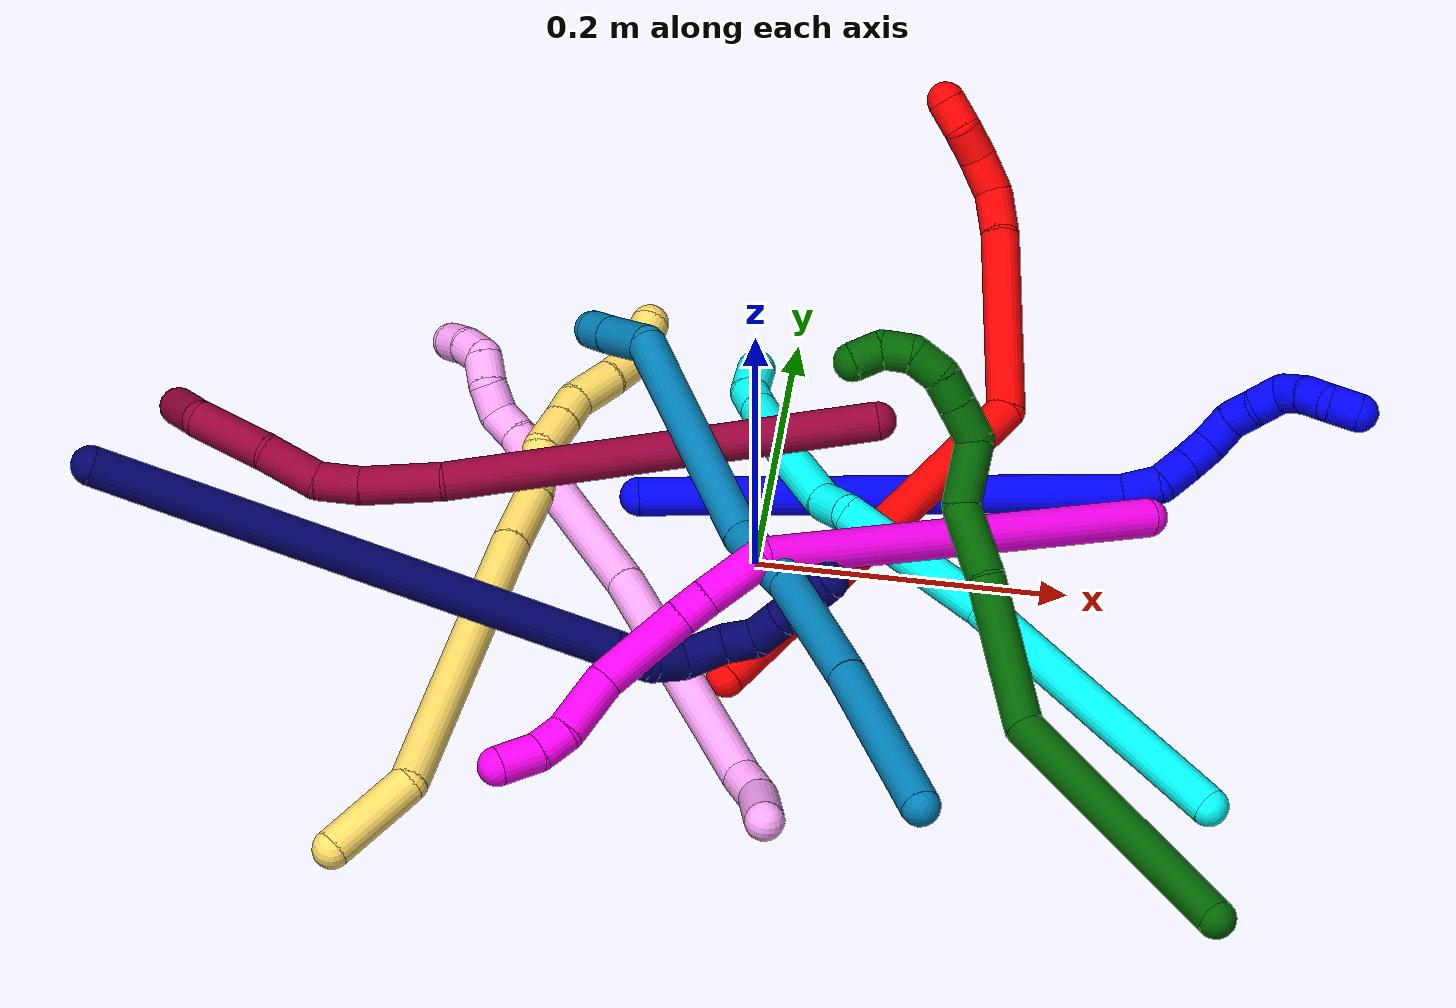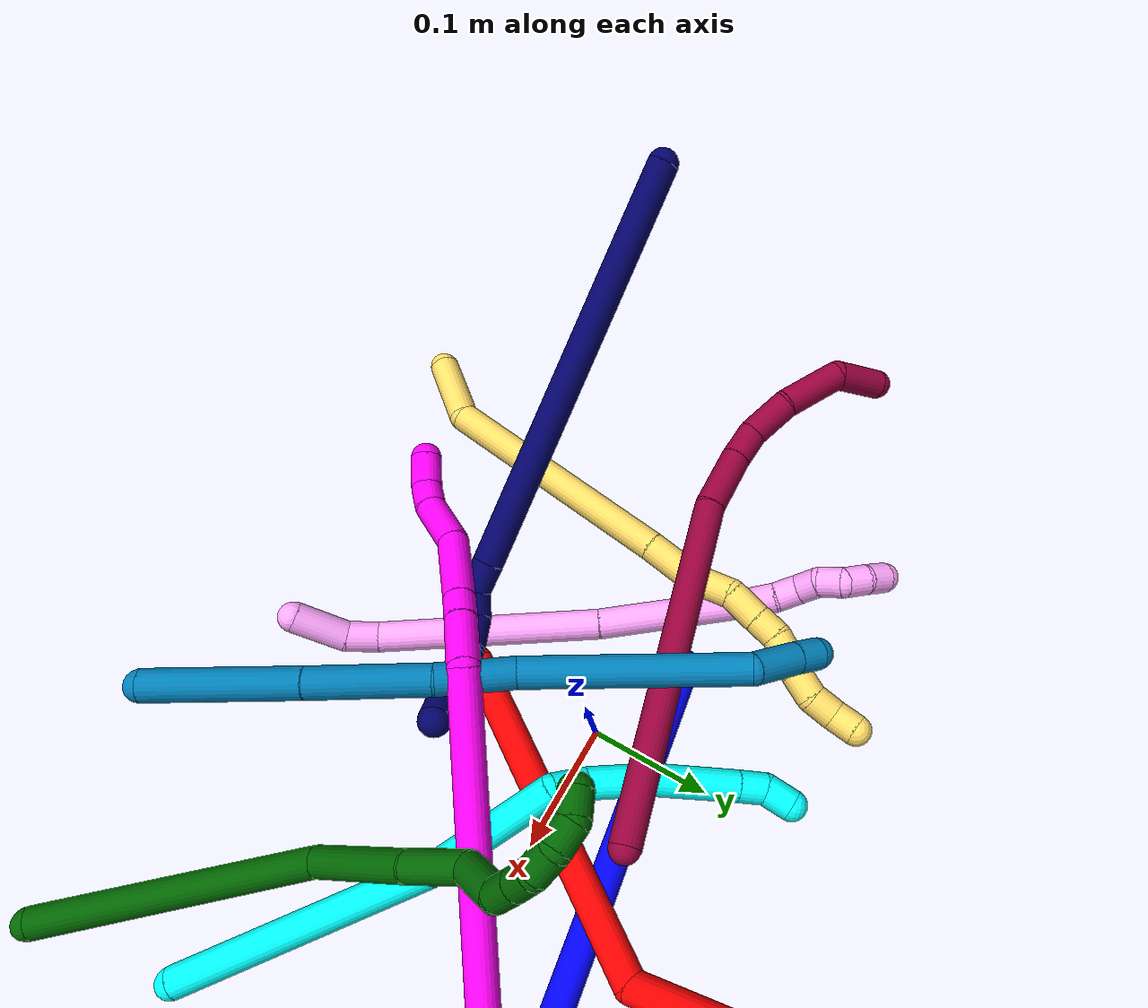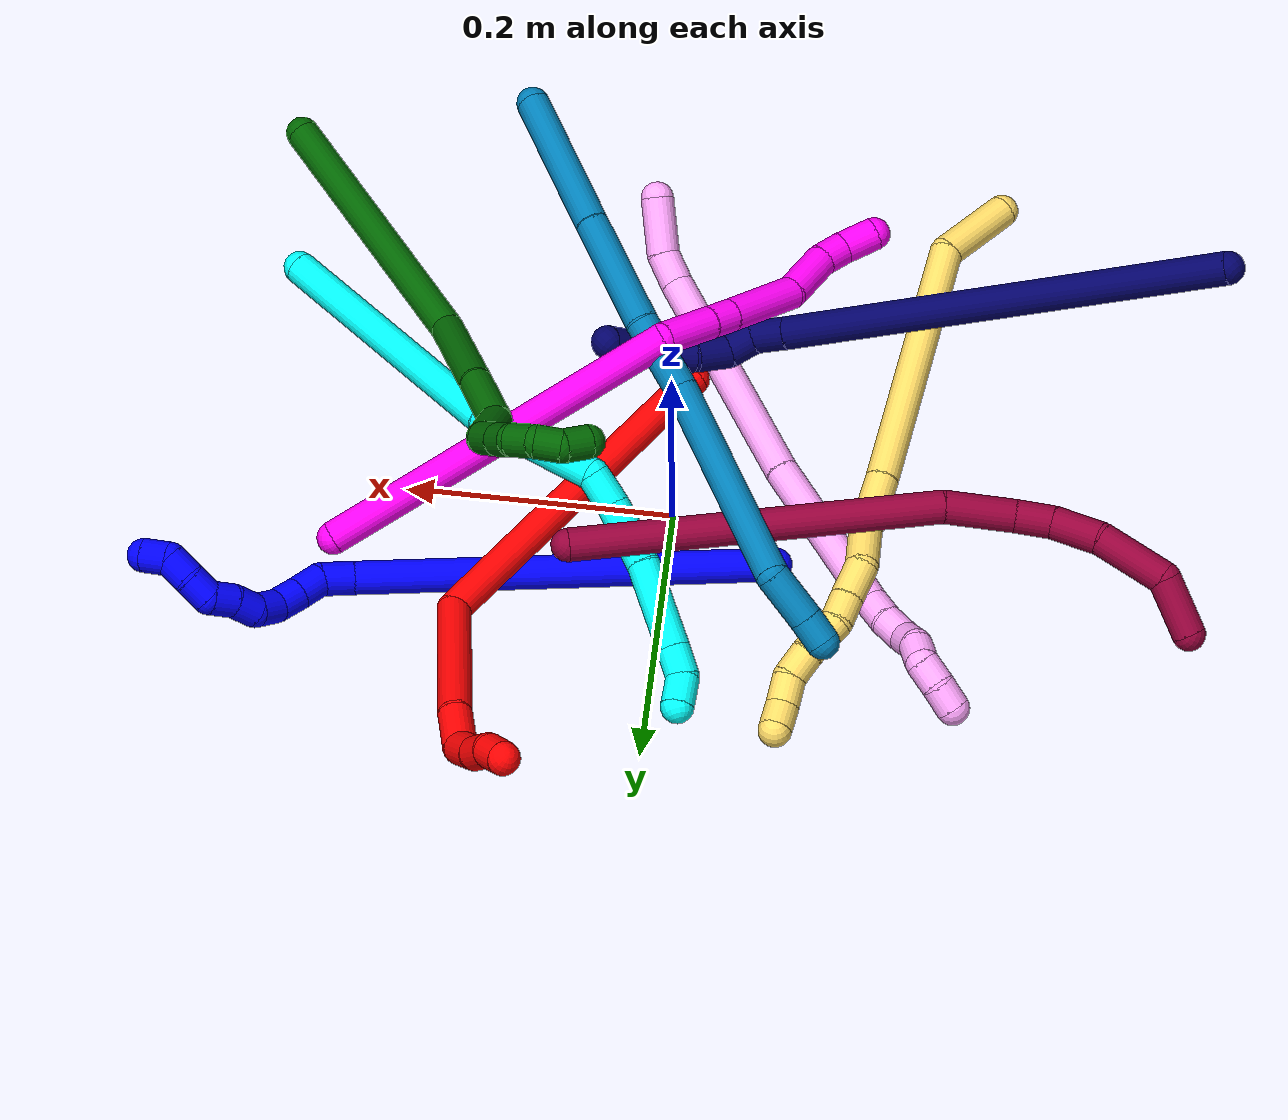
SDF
<sdf version="1.7">
 <world name="default">
  <plugin name="TubeGeneratorPlugin" filename="libtube_generator_plugin.so"/>
  <model name="photoneo_s_sensor">
   <static>1</static>
   <pose>0 0 2 1.57079 1.57079 3.14159</pose>
   <link name="link">
    <inertial><mass>0.1</mass></inertial>
    <sensor name="sensor" type="depth">
     <update_rate>30</update_rate>
     <camera>
      <horizontal_fov>1.22</horizontal_fov>
      <image><width>1920</width><height>1200</height><format>B8G8R8</format></image>
      <clip><near>0.1</near><far>4</far></clip>
      <depth_camera><output>points</output></depth_camera>
     </camera>
     <plugin name="camera_plugin" filename="libgazebo_ros_depth_camera.so">
      <baseline>0.2</baseline>
      <alwaysOn>1</alwaysOn>
      <updateRate>0.0</updateRate>
      <cameraName>camera_ir</cameraName>
      <imageTopicName>/camera/color/image_raw</imageTopicName>
      <cameraInfoTopicName>/camera/color/camera_info</cameraInfoTopicName>
      <depthImageTopicName>/camera/depth/image_raw</depthImageTopicName>
      <depthImageCameraInfoTopicName>/camera/depth/camera_info</depthImageCameraInfoTopicName>
      <pointCloudTopicName>/camera/depth/points</pointCloudTopicName>
      <frameName>fr_optical</frameName>
      <pointCloudCutoff>0.1</pointCloudCutoff>
      <pointCloudCutoffMax>2.0</pointCloudCutoffMax>
      <distortionK1>0</distortionK1>
      <distortionK2>0</distortionK2>
      <distortionK3>0</distortionK3>
      <distortionT1>0</distortionT1>
      <distortionT2>0</distortionT2>
      <CxPrime>0</CxPrime>
      <Cx>0</Cx>
      <Cy>0</Cy>
      <focalLength>0</focalLength>
      <hackBaseline>0</hackBaseline>
     </plugin>
    </sensor>
   </link>
  </model>
  <gravity>0 0 -9.8</gravity>
  <magnetic_field>6e-06 2.3e-05 -4.2e-05</magnetic_field>
  <atmosphere type="adiabatic"/>
  <physics name="default_physics" default="0" type="ode">
   <max_step_size>0.003</max_step_size>
   <real_time_factor>1</real_time_factor>
   <real_time_update_rate>1000</real_time_update_rate>
   <max_contacts>10000</max_contacts>
   <ode>
    <solver>
     <type>quick</type>
     <iters>100</iters>
     <sor>1.3</sor>
     <use_dynamic_moi_rescaling>0</use_dynamic_moi_rescaling>
    </solver>
    <constraints>
     <contact_max_correcting_vel>0</contact_max_correcting_vel>
     <contact_surface_layer>0.001</contact_surface_layer>
     <cfm>0</cfm>
     <erp>0.2</erp>
    </constraints>
   </ode>
  </physics>
  <scene><ambient>0.4 0.4 0.4 1</ambient><background>0.7 0.7 0.7 1</background><shadows>0</shadows></scene>
  <audio><device>default</device></audio>
  <spherical_coordinates>
   <surface_model>EARTH_WGS84</surface_model>
   <latitude_deg>0</latitude_deg>
   <longitude_deg>0</longitude_deg>
   <elevation>0</elevation>
   <heading_deg>0</heading_deg>
  </spherical_coordinates>
  <model name="bin">
   <static>1</static>
   <link name="bottom">
    <collision name="collision-bottom">
     <pose>0 0 -0.01 0 -0 0</pose>
     <geometry><box><size>0.8 0.6 0.02</size></box></geometry>
     <surface>
      <friction><ode><mu>100</mu><mu2>100</mu2></ode></friction>
      <contact><collide_bitmask>65535</collide_bitmask></contact>
     </surface>
    </collision>
   </link>
   <link name="west_wall">
    <collision name="collision-west_wall">
     <pose>-0.41 0 0.1 0 -0 0</pose>
     <geometry><box><size>0.02 0.6 0.2</size></box></geometry>
     <surface>
      <friction><ode><mu>100</mu><mu2>100</mu2></ode></friction>
      <contact><collide_bitmask>65535</collide_bitmask></contact>
     </surface>
    </collision>
   </link>
   <link name="east_wall">
    <collision name="collision-east_wall">
     <pose>0.41 0 0.1 0 -0 0</pose>
     <geometry><box><size>0.02 0.6 0.2</size></box></geometry>
     <surface>
      <friction><ode><mu>100</mu><mu2>100</mu2></ode></friction>
      <contact><collide_bitmask>65535</collide_bitmask></contact>
     </surface>
    </collision>
   </link>
   <link name="south_wall">
    <collision name="collision-south_wall">
     <pose>0 -0.31 0.1 0 -0 0</pose>
     <geometry><box><size>0.8 0.02 0.2</size></box></geometry>
     <surface>
      <friction><ode><mu>100</mu><mu2>100</mu2></ode></friction>
      <contact><collide_bitmask>65535</collide_bitmask></contact>
     </surface>
    </collision>
   </link>
   <link name="north_wall">
    <collision name="collision-north_wall">
     <pose>0 0.31 0.1 0 -0 0</pose>
     <geometry><box><size>0.8 0.02 0.2</size></box></geometry>
     <surface>
      <friction><ode><mu>100</mu><mu2>100</mu2></ode></friction>
      <contact><collide_bitmask>65535</collide_bitmask></contact>
     </surface>
    </collision>
   </link>
  </model>
  <model name="1">
   <static>0</static>
   <link name="1">
    <collision name="collision-cylinder-e_1_1_4">
     <pose>0.133681 0.030299 0.073276 -0.392083 1.03542 -0.22525</pose>
     <geometry><cylinder><radius>0.0125</radius><length>0.310857</length></cylinder></geometry>
     <surface>
      <friction><ode><mu>1.16</mu><mu2>1.16</mu2><slip1>0</slip1><slip2>0</slip2></ode></friction>
      <contact><ode><kp>1e+06</kp><kd>1</kd><max_vel>0</max_vel><min_depth>0.001</min_depth></ode></contact>
     </surface>
    </collision>
    <visual name="visual-cylinder-e_1_1_4">
     <pose>0.133681 0.030299 0.073276 -0.392083 1.03542 -0.22525</pose>
     <geometry><cylinder><radius>0.0125</radius><length>0.310857</length></cylinder></geometry>
     <material><ambient>0 0 1 1</ambient></material>
    </visual>
    <collision name="collision-cylinder-e_2_4_5">
     <pose>0.277868 0.060341 0.153365 0.037789 0.995255 0.020529</pose>
     <geometry><cylinder><radius>0.0125</radius><length>0.025048</length></cylinder></geometry>
     <surface>
      <friction><ode><mu>1.16</mu><mu2>1.16</mu2><slip1>0</slip1><slip2>0</slip2></ode></friction>
      <contact><ode><kp>1e+06</kp><kd>1</kd><max_vel>0</max_vel><min_depth>0.001</min_depth></ode></contact>
     </surface>
    </collision>
    <visual name="visual-cylinder-e_2_4_5">
     <pose>0.277868 0.060341 0.153365 0.037789 0.995255 0.020529</pose>
     <geometry><cylinder><radius>0.0125</radius><length>0.025048</length></cylinder></geometry>
     <material><ambient>0 0 1 1</ambient></material>
    </visual>
    <collision name="collision-cylinder-e_3_5_6">
     <pose>0.293063 0.058415 0.169955 0.16894 0.441566 0.038003</pose>
     <geometry><cylinder><radius>0.0125</radius><length>0.021945</length></cylinder></geometry>
     <surface>
      <friction><ode><mu>1.16</mu><mu2>1.16</mu2><slip1>0</slip1><slip2>0</slip2></ode></friction>
      <contact><ode><kp>1e+06</kp><kd>1</kd><max_vel>0</max_vel><min_depth>0.001</min_depth></ode></contact>
     </surface>
    </collision>
    <visual name="visual-cylinder-e_3_5_6">
     <pose>0.293063 0.058415 0.169955 0.16894 0.441566 0.038003</pose>
     <geometry><cylinder><radius>0.0125</radius><length>0.021945</length></cylinder></geometry>
     <material><ambient>0 0 1 1</ambient></material>
    </visual>
    <collision name="collision-cylinder-e_4_6_7">
     <pose>0.302303 0.054522 0.188616 0.245529 0.461185 0.057918</pose>
     <geometry><cylinder><radius>0.0125</radius><length>0.02045</length></cylinder></geometry>
     <surface>
      <friction><ode><mu>1.16</mu><mu2>1.16</mu2><slip1>0</slip1><slip2>0</slip2></ode></friction>
      <contact><ode><kp>1e+06</kp><kd>1</kd><max_vel>0</max_vel><min_depth>0.001</min_depth></ode></contact>
     </surface>
    </collision>
    <visual name="visual-cylinder-e_4_6_7">
     <pose>0.302303 0.054522 0.188616 0.245529 0.461185 0.057918</pose>
     <geometry><cylinder><radius>0.0125</radius><length>0.02045</length></cylinder></geometry>
     <material><ambient>0 0 1 1</ambient></material>
    </visual>
    <collision name="collision-cylinder-e_5_7_8">
     <pose>0.312536 0.046696 0.204785 0.65528 0.553842 0.192612</pose>
     <geometry><cylinder><radius>0.0125</radius><length>0.021611</length></cylinder></geometry>
     <surface>
      <friction><ode><mu>1.16</mu><mu2>1.16</mu2><slip1>0</slip1><slip2>0</slip2></ode></friction>
      <contact><ode><kp>1e+06</kp><kd>1</kd><max_vel>0</max_vel><min_depth>0.001</min_depth></ode></contact>
     </surface>
    </collision>
    <visual name="visual-cylinder-e_5_7_8">
     <pose>0.312536 0.046696 0.204785 0.65528 0.553842 0.192612</pose>
     <geometry><cylinder><radius>0.0125</radius><length>0.021611</length></cylinder></geometry>
     <material><ambient>0 0 1 1</ambient></material>
    </visual>
    <collision name="collision-cylinder-e_6_8_9">
     <pose>0.326784 0.036398 0.214335 1.12179 1.02393 0.678704</pose>
     <geometry><cylinder><radius>0.0125</radius><length>0.020054</length></cylinder></geometry>
     <surface>
      <friction><ode><mu>1.16</mu><mu2>1.16</mu2><slip1>0</slip1><slip2>0</slip2></ode></friction>
      <contact><ode><kp>1e+06</kp><kd>1</kd><max_vel>0</max_vel><min_depth>0.001</min_depth></ode></contact>
     </surface>
    </collision>
    <visual name="visual-cylinder-e_6_8_9">
     <pose>0.326784 0.036398 0.214335 1.12179 1.02393 0.678704</pose>
     <geometry><cylinder><radius>0.0125</radius><length>0.020054</length></cylinder></geometry>
     <material><ambient>0 0 1 1</ambient></material>
    </visual>
    <collision name="collision-cylinder-e_7_9_10">
     <pose>0.343446 0.028085 0.221222 0.663645 0.943552 0.348037</pose>
     <geometry><cylinder><radius>0.0125</radius><length>0.020001</length></cylinder></geometry>
     <surface>
      <friction><ode><mu>1.16</mu><mu2>1.16</mu2><slip1>0</slip1><slip2>0</slip2></ode></friction>
      <contact><ode><kp>1e+06</kp><kd>1</kd><max_vel>0</max_vel><min_depth>0.001</min_depth></ode></contact>
     </surface>
    </collision>
    <visual name="visual-cylinder-e_7_9_10">
     <pose>0.343446 0.028085 0.221222 0.663645 0.943552 0.348037</pose>
     <geometry><cylinder><radius>0.0125</radius><length>0.020001</length></cylinder></geometry>
     <material><ambient>0 0 1 1</ambient></material>
    </visual>
    <collision name="collision-cylinder-e_8_10_11">
     <pose>0.36108 0.022346 0.2237 2.36151 1.26425 2.1186</pose>
     <geometry><cylinder><radius>0.0125</radius><length>0.020007</length></cylinder></geometry>
     <surface>
      <friction><ode><mu>1.16</mu><mu2>1.16</mu2><slip1>0</slip1><slip2>0</slip2></ode></friction>
      <contact><ode><kp>1e+06</kp><kd>1</kd><max_vel>0</max_vel><min_depth>0.001</min_depth></ode></contact>
     </surface>
    </collision>
    <visual name="visual-cylinder-e_8_10_11">
     <pose>0.36108 0.022346 0.2237 2.36151 1.26425 2.1186</pose>
     <geometry><cylinder><radius>0.0125</radius><length>0.020007</length></cylinder></geometry>
     <material><ambient>0 0 1 1</ambient></material>
    </visual>
    <collision name="collision-cylinder-e_9_11_12">
     <pose>0.380197 0.02021 0.218651 3.13697 1.27651 3.13536</pose>
     <geometry><cylinder><radius>0.0125</radius><length>0.020021</length></cylinder></geometry>
     <surface>
      <friction><ode><mu>1.16</mu><mu2>1.16</mu2><slip1>0</slip1><slip2>0</slip2></ode></friction>
      <contact><ode><kp>1e+06</kp><kd>1</kd><max_vel>0</max_vel><min_depth>0.001</min_depth></ode></contact>
     </surface>
    </collision>
    <visual name="visual-cylinder-e_9_11_12">
     <pose>0.380197 0.02021 0.218651 3.13697 1.27651 3.13536</pose>
     <geometry><cylinder><radius>0.0125</radius><length>0.020021</length></cylinder></geometry>
     <material><ambient>0 0 1 1</ambient></material>
    </visual>
    <collision name="collision-cylinder-e_10_12_2">
     <pose>0.398678 0.024209 0.217922 -1.07426 1.09696 -0.697975</pose>
     <geometry><cylinder><radius>0.0125</radius><length>0.020006</length></cylinder></geometry>
     <surface>
      <friction><ode><mu>1.16</mu><mu2>1.16</mu2><slip1>0</slip1><slip2>0</slip2></ode></friction>
      <contact><ode><kp>1e+06</kp><kd>1</kd><max_vel>0</max_vel><min_depth>0.001</min_depth></ode></contact>
     </surface>
    </collision>
    <visual name="visual-cylinder-e_10_12_2">
     <pose>0.398678 0.024209 0.217922 -1.07426 1.09696 -0.697975</pose>
     <geometry><cylinder><radius>0.0125</radius><length>0.020006</length></cylinder></geometry>
     <material><ambient>0 0 1 1</ambient></material>
    </visual>
    <collision name="collision-sphere-2">
     <pose>0.407579 0.028223 0.220096 0 -0 0</pose>
     <geometry><sphere><radius>0.0125</radius></sphere></geometry>
     <surface>
      <friction><ode><mu>1.16</mu><mu2>1.16</mu2><slip1>0</slip1><slip2>0</slip2></ode></friction>
      <contact><ode><kp>1e+06</kp><kd>1</kd><max_vel>0</max_vel><min_depth>0.001</min_depth></ode></contact>
     </surface>
    </collision>
    <visual name="visual-sphere-2">
     <pose>0.407579 0.028223 0.220096 0 -0 0</pose>
     <geometry><sphere><radius>0.0125</radius></sphere></geometry>
     <material><ambient>0 0 1 1</ambient></material>
    </visual>
    <collision name="collision-sphere-12">
     <pose>0.389777 0.020196 0.215747 0 -0 0</pose>
     <geometry><sphere><radius>0.0125</radius></sphere></geometry>
     <surface>
      <friction><ode><mu>1.16</mu><mu2>1.16</mu2><slip1>0</slip1><slip2>0</slip2></ode></friction>
      <contact><ode><kp>1e+06</kp><kd>1</kd><max_vel>0</max_vel><min_depth>0.001</min_depth></ode></contact>
     </surface>
    </collision>
    <visual name="visual-sphere-12">
     <pose>0.389777 0.020196 0.215747 0 -0 0</pose>
     <geometry><sphere><radius>0.0125</radius></sphere></geometry>
     <material><ambient>0 0 1 1</ambient></material>
    </visual>
    <collision name="collision-sphere-11">
     <pose>0.370617 0.020223 0.221555 0 -0 0</pose>
     <geometry><sphere><radius>0.0125</radius></sphere></geometry>
     <surface>
      <friction><ode><mu>1.16</mu><mu2>1.16</mu2><slip1>0</slip1><slip2>0</slip2></ode></friction>
      <contact><ode><kp>1e+06</kp><kd>1</kd><max_vel>0</max_vel><min_depth>0.001</min_depth></ode></contact>
     </surface>
    </collision>
    <visual name="visual-sphere-11">
     <pose>0.370617 0.020223 0.221555 0 -0 0</pose>
     <geometry><sphere><radius>0.0125</radius></sphere></geometry>
     <material><ambient>0 0 1 1</ambient></material>
    </visual>
    <collision name="collision-sphere-10">
     <pose>0.351543 0.024469 0.225846 0 -0 0</pose>
     <geometry><sphere><radius>0.0125</radius></sphere></geometry>
     <surface>
      <friction><ode><mu>1.16</mu><mu2>1.16</mu2><slip1>0</slip1><slip2>0</slip2></ode></friction>
      <contact><ode><kp>1e+06</kp><kd>1</kd><max_vel>0</max_vel><min_depth>0.001</min_depth></ode></contact>
     </surface>
    </collision>
    <visual name="visual-sphere-10">
     <pose>0.351543 0.024469 0.225846 0 -0 0</pose>
     <geometry><sphere><radius>0.0125</radius></sphere></geometry>
     <material><ambient>0 0 1 1</ambient></material>
    </visual>
    <collision name="collision-sphere-9">
     <pose>0.335349 0.031701 0.216599 0 -0 0</pose>
     <geometry><sphere><radius>0.0125</radius></sphere></geometry>
     <surface>
      <friction><ode><mu>1.16</mu><mu2>1.16</mu2><slip1>0</slip1><slip2>0</slip2></ode></friction>
      <contact><ode><kp>1e+06</kp><kd>1</kd><max_vel>0</max_vel><min_depth>0.001</min_depth></ode></contact>
     </surface>
    </collision>
    <visual name="visual-sphere-9">
     <pose>0.335349 0.031701 0.216599 0 -0 0</pose>
     <geometry><sphere><radius>0.0125</radius></sphere></geometry>
     <material><ambient>0 0 1 1</ambient></material>
    </visual>
    <collision name="collision-sphere-4">
     <pose>0.267361 0.060598 0.146553 0 -0 0</pose>
     <geometry><sphere><radius>0.0125</radius></sphere></geometry>
     <surface>
      <friction><ode><mu>1.16</mu><mu2>1.16</mu2><slip1>0</slip1><slip2>0</slip2></ode></friction>
      <contact><ode><kp>1e+06</kp><kd>1</kd><max_vel>0</max_vel><min_depth>0.001</min_depth></ode></contact>
     </surface>
    </collision>
    <visual name="visual-sphere-4">
     <pose>0.267361 0.060598 0.146553 0 -0 0</pose>
     <geometry><sphere><radius>0.0125</radius></sphere></geometry>
     <material><ambient>0 0 1 1</ambient></material>
    </visual>
    <collision name="collision-sphere-1">
     <geometry><sphere><radius>0.0125</radius></sphere></geometry>
     <surface>
      <friction><ode><mu>1.16</mu><mu2>1.16</mu2><slip1>0</slip1><slip2>0</slip2></ode></friction>
      <contact><ode><kp>1e+06</kp><kd>1</kd><max_vel>0</max_vel><min_depth>0.001</min_depth></ode></contact>
     </surface>
    </collision>
    <visual name="visual-sphere-1">
     <geometry><sphere><radius>0.0125</radius></sphere></geometry>
     <material><ambient>0 0 1 1</ambient></material>
    </visual>
    <collision name="collision-sphere-8">
     <pose>0.31822 0.041095 0.212072 0 -0 0</pose>
     <geometry><sphere><radius>0.0125</radius></sphere></geometry>
     <surface>
      <friction><ode><mu>1.16</mu><mu2>1.16</mu2><slip1>0</slip1><slip2>0</slip2></ode></friction>
      <contact><ode><kp>1e+06</kp><kd>1</kd><max_vel>0</max_vel><min_depth>0.001</min_depth></ode></contact>
     </surface>
    </collision>
    <visual name="visual-sphere-8">
     <pose>0.31822 0.041095 0.212072 0 -0 0</pose>
     <geometry><sphere><radius>0.0125</radius></sphere></geometry>
     <material><ambient>0 0 1 1</ambient></material>
    </visual>
    <collision name="collision-sphere-5">
     <pose>0.288374 0.060083 0.160176 0 -0 0</pose>
     <geometry><sphere><radius>0.0125</radius></sphere></geometry>
     <surface>
      <friction><ode><mu>1.16</mu><mu2>1.16</mu2><slip1>0</slip1><slip2>0</slip2></ode></friction>
      <contact><ode><kp>1e+06</kp><kd>1</kd><max_vel>0</max_vel><min_depth>0.001</min_depth></ode></contact>
     </surface>
    </collision>
    <visual name="visual-sphere-5">
     <pose>0.288374 0.060083 0.160176 0 -0 0</pose>
     <geometry><sphere><radius>0.0125</radius></sphere></geometry>
     <material><ambient>0 0 1 1</ambient></material>
    </visual>
    <collision name="collision-sphere-6">
     <pose>0.297752 0.056747 0.179734 0 -0 0</pose>
     <geometry><sphere><radius>0.0125</radius></sphere></geometry>
     <surface>
      <friction><ode><mu>1.16</mu><mu2>1.16</mu2><slip1>0</slip1><slip2>0</slip2></ode></friction>
      <contact><ode><kp>1e+06</kp><kd>1</kd><max_vel>0</max_vel><min_depth>0.001</min_depth></ode></contact>
     </surface>
    </collision>
    <visual name="visual-sphere-6">
     <pose>0.297752 0.056747 0.179734 0 -0 0</pose>
     <geometry><sphere><radius>0.0125</radius></sphere></geometry>
     <material><ambient>0 0 1 1</ambient></material>
    </visual>
    <collision name="collision-sphere-7">
     <pose>0.306853 0.052296 0.197499 0 -0 0</pose>
     <geometry><sphere><radius>0.0125</radius></sphere></geometry>
     <surface>
      <friction><ode><mu>1.16</mu><mu2>1.16</mu2><slip1>0</slip1><slip2>0</slip2></ode></friction>
      <contact><ode><kp>1e+06</kp><kd>1</kd><max_vel>0</max_vel><min_depth>0.001</min_depth></ode></contact>
     </surface>
    </collision>
    <visual name="visual-sphere-7">
     <pose>0.306853 0.052296 0.197499 0 -0 0</pose>
     <geometry><sphere><radius>0.0125</radius></sphere></geometry>
     <material><ambient>0 0 1 1</ambient></material>
    </visual>
    <inertial>
     <pose>0.208236 0.033928 0.121137 0 -0 0</pose>
     <mass>0.5</mass>
     <inertia>
      <ixx>0.001004</ixx>
      <ixy>0</ixy>
      <ixz>0</ixz>
      <iyy>0.002181</iyy>
      <iyz>0</iyz>
      <izz>-0.002645</izz>
     </inertia>
    </inertial>
   </link>
   <pose>-0.081038 0.037521 0.011498 -1.65524 -0.265643 -0.317144</pose>
  </model>
  <model name="2">
   <static>0</static>
   <link name="2">
    <collision name="collision-cylinder-e_1_1_4">
     <pose>0.056743 0.125308 -0.009512 -1.64656 0.424122 -0.456428</pose>
     <geometry><cylinder><radius>0.0125</radius><length>0.275771</length></cylinder></geometry>
     <surface>
      <friction><ode><mu>1.16</mu><mu2>1.16</mu2><slip1>0</slip1><slip2>0</slip2></ode></friction>
      <contact><ode><kp>1e+06</kp><kd>1</kd><max_vel>0</max_vel><min_depth>0.001</min_depth></ode></contact>
     </surface>
    </collision>
    <visual name="visual-cylinder-e_1_1_4">
     <pose>0.056743 0.125308 -0.009512 -1.64656 0.424122 -0.456428</pose>
     <geometry><cylinder><radius>0.0125</radius><length>0.275771</length></cylinder></geometry>
     <material><ambient>1 0 0 1</ambient></material>
    </visual>
    <collision name="collision-cylinder-e_2_4_5">
     <pose>0.109014 0.303296 0.012029 -1.03815 -0.072996 0.041718</pose>
     <geometry><cylinder><radius>0.0125</radius><length>0.122627</length></cylinder></geometry>
     <surface>
      <friction><ode><mu>1.16</mu><mu2>1.16</mu2><slip1>0</slip1><slip2>0</slip2></ode></friction>
      <contact><ode><kp>1e+06</kp><kd>1</kd><max_vel>0</max_vel><min_depth>0.001</min_depth></ode></contact>
     </surface>
    </collision>
    <visual name="visual-cylinder-e_2_4_5">
     <pose>0.109014 0.303296 0.012029 -1.03815 -0.072996 0.041718</pose>
     <geometry><cylinder><radius>0.0125</radius><length>0.122627</length></cylinder></geometry>
     <material><ambient>1 0 0 1</ambient></material>
    </visual>
    <collision name="collision-cylinder-e_3_5_6">
     <pose>0.100673 0.370098 0.049565 -1.14047 -0.244006 0.156939</pose>
     <geometry><cylinder><radius>0.0125</radius><length>0.032028</length></cylinder></geometry>
     <surface>
      <friction><ode><mu>1.16</mu><mu2>1.16</mu2><slip1>0</slip1><slip2>0</slip2></ode></friction>
      <contact><ode><kp>1e+06</kp><kd>1</kd><max_vel>0</max_vel><min_depth>0.001</min_depth></ode></contact>
     </surface>
    </collision>
    <visual name="visual-cylinder-e_3_5_6">
     <pose>0.100673 0.370098 0.049565 -1.14047 -0.244006 0.156939</pose>
     <geometry><cylinder><radius>0.0125</radius><length>0.032028</length></cylinder></geometry>
     <material><ambient>1 0 0 1</ambient></material>
    </visual>
    <collision name="collision-cylinder-e_4_6_7">
     <pose>0.094393 0.389488 0.068097 -0.412124 -0.181364 0.03801</pose>
     <geometry><cylinder><radius>0.0125</radius><length>0.026739</length></cylinder></geometry>
     <surface>
      <friction><ode><mu>1.16</mu><mu2>1.16</mu2><slip1>0</slip1><slip2>0</slip2></ode></friction>
      <contact><ode><kp>1e+06</kp><kd>1</kd><max_vel>0</max_vel><min_depth>0.001</min_depth></ode></contact>
     </surface>
    </collision>
    <visual name="visual-cylinder-e_4_6_7">
     <pose>0.094393 0.389488 0.068097 -0.412124 -0.181364 0.03801</pose>
     <geometry><cylinder><radius>0.0125</radius><length>0.026739</length></cylinder></geometry>
     <material><ambient>1 0 0 1</ambient></material>
    </visual>
    <collision name="collision-cylinder-e_5_7_8">
     <pose>0.090778 0.396566 0.091198 -0.16239 -0.107019 0.008717</pose>
     <geometry><cylinder><radius>0.0125</radius><length>0.022528</length></cylinder></geometry>
     <surface>
      <friction><ode><mu>1.16</mu><mu2>1.16</mu2><slip1>0</slip1><slip2>0</slip2></ode></friction>
      <contact><ode><kp>1e+06</kp><kd>1</kd><max_vel>0</max_vel><min_depth>0.001</min_depth></ode></contact>
     </surface>
    </collision>
    <visual name="visual-cylinder-e_5_7_8">
     <pose>0.090778 0.396566 0.091198 -0.16239 -0.107019 0.008717</pose>
     <geometry><cylinder><radius>0.0125</radius><length>0.022528</length></cylinder></geometry>
     <material><ambient>1 0 0 1</ambient></material>
    </visual>
    <collision name="collision-cylinder-e_6_8_2">
     <pose>0.086194 0.402821 0.110731 -0.482681 -0.339438 0.08431</pose>
     <geometry><cylinder><radius>0.0125</radius><length>0.020307</length></cylinder></geometry>
     <surface>
      <friction><ode><mu>1.16</mu><mu2>1.16</mu2><slip1>0</slip1><slip2>0</slip2></ode></friction>
      <contact><ode><kp>1e+06</kp><kd>1</kd><max_vel>0</max_vel><min_depth>0.001</min_depth></ode></contact>
     </surface>
    </collision>
    <visual name="visual-cylinder-e_6_8_2">
     <pose>0.086194 0.402821 0.110731 -0.482681 -0.339438 0.08431</pose>
     <geometry><cylinder><radius>0.0125</radius><length>0.020307</length></cylinder></geometry>
     <material><ambient>1 0 0 1</ambient></material>
    </visual>
    <collision name="collision-sphere-2">
     <pose>0.082814 0.407264 0.119211 0 -0 0</pose>
     <geometry><sphere><radius>0.0125</radius></sphere></geometry>
     <surface>
      <friction><ode><mu>1.16</mu><mu2>1.16</mu2><slip1>0</slip1><slip2>0</slip2></ode></friction>
      <contact><ode><kp>1e+06</kp><kd>1</kd><max_vel>0</max_vel><min_depth>0.001</min_depth></ode></contact>
     </surface>
    </collision>
    <visual name="visual-sphere-2">
     <pose>0.082814 0.407264 0.119211 0 -0 0</pose>
     <geometry><sphere><radius>0.0125</radius></sphere></geometry>
     <material><ambient>1 0 0 1</ambient></material>
    </visual>
    <collision name="collision-sphere-4">
     <pose>0.113486 0.250617 -0.019024 0 -0 0</pose>
     <geometry><sphere><radius>0.0125</radius></sphere></geometry>
     <surface>
      <friction><ode><mu>1.16</mu><mu2>1.16</mu2><slip1>0</slip1><slip2>0</slip2></ode></friction>
      <contact><ode><kp>1e+06</kp><kd>1</kd><max_vel>0</max_vel><min_depth>0.001</min_depth></ode></contact>
     </surface>
    </collision>
    <visual name="visual-sphere-4">
     <pose>0.113486 0.250617 -0.019024 0 -0 0</pose>
     <geometry><sphere><radius>0.0125</radius></sphere></geometry>
     <material><ambient>1 0 0 1</ambient></material>
    </visual>
    <collision name="collision-sphere-1">
     <geometry><sphere><radius>0.0125</radius></sphere></geometry>
     <surface>
      <friction><ode><mu>1.16</mu><mu2>1.16</mu2><slip1>0</slip1><slip2>0</slip2></ode></friction>
      <contact><ode><kp>1e+06</kp><kd>1</kd><max_vel>0</max_vel><min_depth>0.001</min_depth></ode></contact>
     </surface>
    </collision>
    <visual name="visual-sphere-1">
     <geometry><sphere><radius>0.0125</radius></sphere></geometry>
     <material><ambient>1 0 0 1</ambient></material>
    </visual>
    <collision name="collision-sphere-8">
     <pose>0.089575 0.398377 0.102251 0 -0 0</pose>
     <geometry><sphere><radius>0.0125</radius></sphere></geometry>
     <surface>
      <friction><ode><mu>1.16</mu><mu2>1.16</mu2><slip1>0</slip1><slip2>0</slip2></ode></friction>
      <contact><ode><kp>1e+06</kp><kd>1</kd><max_vel>0</max_vel><min_depth>0.001</min_depth></ode></contact>
     </surface>
    </collision>
    <visual name="visual-sphere-8">
     <pose>0.089575 0.398377 0.102251 0 -0 0</pose>
     <geometry><sphere><radius>0.0125</radius></sphere></geometry>
     <material><ambient>1 0 0 1</ambient></material>
    </visual>
    <collision name="collision-sphere-5">
     <pose>0.104542 0.355975 0.043082 0 -0 0</pose>
     <geometry><sphere><radius>0.0125</radius></sphere></geometry>
     <surface>
      <friction><ode><mu>1.16</mu><mu2>1.16</mu2><slip1>0</slip1><slip2>0</slip2></ode></friction>
      <contact><ode><kp>1e+06</kp><kd>1</kd><max_vel>0</max_vel><min_depth>0.001</min_depth></ode></contact>
     </surface>
    </collision>
    <visual name="visual-sphere-5">
     <pose>0.104542 0.355975 0.043082 0 -0 0</pose>
     <geometry><sphere><radius>0.0125</radius></sphere></geometry>
     <material><ambient>1 0 0 1</ambient></material>
    </visual>
    <collision name="collision-sphere-6">
     <pose>0.096804 0.38422 0.056047 0 -0 0</pose>
     <geometry><sphere><radius>0.0125</radius></sphere></geometry>
     <surface>
      <friction><ode><mu>1.16</mu><mu2>1.16</mu2><slip1>0</slip1><slip2>0</slip2></ode></friction>
      <contact><ode><kp>1e+06</kp><kd>1</kd><max_vel>0</max_vel><min_depth>0.001</min_depth></ode></contact>
     </surface>
    </collision>
    <visual name="visual-sphere-6">
     <pose>0.096804 0.38422 0.056047 0 -0 0</pose>
     <geometry><sphere><radius>0.0125</radius></sphere></geometry>
     <material><ambient>1 0 0 1</ambient></material>
    </visual>
    <collision name="collision-sphere-7">
     <pose>0.091981 0.394755 0.080146 0 -0 0</pose>
     <geometry><sphere><radius>0.0125</radius></sphere></geometry>
     <surface>
      <friction><ode><mu>1.16</mu><mu2>1.16</mu2><slip1>0</slip1><slip2>0</slip2></ode></friction>
      <contact><ode><kp>1e+06</kp><kd>1</kd><max_vel>0</max_vel><min_depth>0.001</min_depth></ode></contact>
     </surface>
    </collision>
    <visual name="visual-sphere-7">
     <pose>0.091981 0.394755 0.080146 0 -0 0</pose>
     <geometry><sphere><radius>0.0125</radius></sphere></geometry>
     <material><ambient>1 0 0 1</ambient></material>
    </visual>
    <inertial>
     <pose>0.07712 0.222261 0.013127 0 -0 0</pose>
     <mass>0.5</mass>
     <inertia>
      <ixx>0.000914</ixx>
      <ixy>0</ixy>
      <ixz>0</ixz>
      <iyy>-0.00038</iyy>
      <iyz>0</iyz>
      <izz>-0.00244</izz>
     </inertia>
    </inertial>
   </link>
   <pose>-0.002339 -0.112538 0.012364 -0.01159 -0.452595 -0.152545</pose>
  </model>
  <model name="3">
   <static>0</static>
   <link name="3">
    <collision name="collision-cylinder-e_1_1_4">
     <pose>-0.049425 0.033452 -0.081681 -2.75289 -0.510453 1.84897</pose>
     <geometry><cylinder><radius>0.0125</radius><length>0.202323</length></cylinder></geometry>
     <surface>
      <friction><ode><mu>1.16</mu><mu2>1.16</mu2><slip1>0</slip1><slip2>0</slip2></ode></friction>
      <contact><ode><kp>1e+06</kp><kd>1</kd><max_vel>0</max_vel><min_depth>0.001</min_depth></ode></contact>
     </surface>
    </collision>
    <visual name="visual-cylinder-e_1_1_4">
     <pose>-0.049425 0.033452 -0.081681 -2.75289 -0.510453 1.84897</pose>
     <geometry><cylinder><radius>0.0125</radius><length>0.202323</length></cylinder></geometry>
     <material><ambient>0.003922 1 0.996078 1</ambient></material>
    </visual>
    <collision name="collision-cylinder-e_2_4_5">
     <pose>-0.131703 0.087888 -0.199571 -2.61635 -0.665549 1.81948</pose>
     <geometry><cylinder><radius>0.0125</radius><length>0.106409</length></cylinder></geometry>
     <surface>
      <friction><ode><mu>1.16</mu><mu2>1.16</mu2><slip1>0</slip1><slip2>0</slip2></ode></friction>
      <contact><ode><kp>1e+06</kp><kd>1</kd><max_vel>0</max_vel><min_depth>0.001</min_depth></ode></contact>
     </surface>
    </collision>
    <visual name="visual-cylinder-e_2_4_5">
     <pose>-0.131703 0.087888 -0.199571 -2.61635 -0.665549 1.81948</pose>
     <geometry><cylinder><radius>0.0125</radius><length>0.106409</length></cylinder></geometry>
     <material><ambient>0.003922 1 0.996078 1</ambient></material>
    </visual>
    <collision name="collision-cylinder-e_3_5_6">
     <pose>-0.169592 0.10661 -0.248463 2.96508 -0.372579 -2.26371</pose>
     <geometry><cylinder><radius>0.0125</radius><length>0.027665</length></cylinder></geometry>
     <surface>
      <friction><ode><mu>1.16</mu><mu2>1.16</mu2><slip1>0</slip1><slip2>0</slip2></ode></friction>
      <contact><ode><kp>1e+06</kp><kd>1</kd><max_vel>0</max_vel><min_depth>0.001</min_depth></ode></contact>
     </surface>
    </collision>
    <visual name="visual-cylinder-e_3_5_6">
     <pose>-0.169592 0.10661 -0.248463 2.96508 -0.372579 -2.26371</pose>
     <geometry><cylinder><radius>0.0125</radius><length>0.027665</length></cylinder></geometry>
     <material><ambient>0.003922 1 0.996078 1</ambient></material>
    </visual>
    <collision name="collision-cylinder-e_4_6_7">
     <pose>-0.180015 0.106351 -0.285437 -3.05929 -0.217568 2.42054</pose>
     <geometry><cylinder><radius>0.0125</radius><length>0.049923</length></cylinder></geometry>
     <surface>
      <friction><ode><mu>1.16</mu><mu2>1.16</mu2><slip1>0</slip1><slip2>0</slip2></ode></friction>
      <contact><ode><kp>1e+06</kp><kd>1</kd><max_vel>0</max_vel><min_depth>0.001</min_depth></ode></contact>
     </surface>
    </collision>
    <visual name="visual-cylinder-e_4_6_7">
     <pose>-0.180015 0.106351 -0.285437 -3.05929 -0.217568 2.42054</pose>
     <geometry><cylinder><radius>0.0125</radius><length>0.049923</length></cylinder></geometry>
     <material><ambient>0.003922 1 0.996078 1</ambient></material>
    </visual>
    <collision name="collision-cylinder-e_5_7_8">
     <pose>-0.18876 0.108485 -0.343318 -3.13771 -0.099592 3.06374</pose>
     <geometry><cylinder><radius>0.0125</radius><length>0.067515</length></cylinder></geometry>
     <surface>
      <friction><ode><mu>1.16</mu><mu2>1.16</mu2><slip1>0</slip1><slip2>0</slip2></ode></friction>
      <contact><ode><kp>1e+06</kp><kd>1</kd><max_vel>0</max_vel><min_depth>0.001</min_depth></ode></contact>
     </surface>
    </collision>
    <visual name="visual-cylinder-e_5_7_8">
     <pose>-0.18876 0.108485 -0.343318 -3.13771 -0.099592 3.06374</pose>
     <geometry><cylinder><radius>0.0125</radius><length>0.067515</length></cylinder></geometry>
     <material><ambient>0.003922 1 0.996078 1</ambient></material>
    </visual>
    <collision name="collision-cylinder-e_6_8_9">
     <pose>-0.192982 0.108764 -0.388132 -3.12836 -0.077013 2.8015</pose>
     <geometry><cylinder><radius>0.0125</radius><length>0.022516</length></cylinder></geometry>
     <surface>
      <friction><ode><mu>1.16</mu><mu2>1.16</mu2><slip1>0</slip1><slip2>0</slip2></ode></friction>
      <contact><ode><kp>1e+06</kp><kd>1</kd><max_vel>0</max_vel><min_depth>0.001</min_depth></ode></contact>
     </surface>
    </collision>
    <visual name="visual-cylinder-e_6_8_9">
     <pose>-0.192982 0.108764 -0.388132 -3.12836 -0.077013 2.8015</pose>
     <geometry><cylinder><radius>0.0125</radius><length>0.022516</length></cylinder></geometry>
     <material><ambient>0.003922 1 0.996078 1</ambient></material>
    </visual>
    <collision name="collision-cylinder-e_7_9_2">
     <pose>-0.189046 0.110507 -0.410042 -2.99347 0.418234 -2.46891</pose>
     <geometry><cylinder><radius>0.0125</radius><length>0.023648</length></cylinder></geometry>
     <surface>
      <friction><ode><mu>1.16</mu><mu2>1.16</mu2><slip1>0</slip1><slip2>0</slip2></ode></friction>
      <contact><ode><kp>1e+06</kp><kd>1</kd><max_vel>0</max_vel><min_depth>0.001</min_depth></ode></contact>
     </surface>
    </collision>
    <visual name="visual-cylinder-e_7_9_2">
     <pose>-0.189046 0.110507 -0.410042 -2.99347 0.418234 -2.46891</pose>
     <geometry><cylinder><radius>0.0125</radius><length>0.023648</length></cylinder></geometry>
     <material><ambient>0.003922 1 0.996078 1</ambient></material>
    </visual>
    <collision name="collision-sphere-2">
     <pose>-0.184244 0.112102 -0.420728 0 -0 0</pose>
     <geometry><sphere><radius>0.0125</radius></sphere></geometry>
     <surface>
      <friction><ode><mu>1.16</mu><mu2>1.16</mu2><slip1>0</slip1><slip2>0</slip2></ode></friction>
      <contact><ode><kp>1e+06</kp><kd>1</kd><max_vel>0</max_vel><min_depth>0.001</min_depth></ode></contact>
     </surface>
    </collision>
    <visual name="visual-sphere-2">
     <pose>-0.184244 0.112102 -0.420728 0 -0 0</pose>
     <geometry><sphere><radius>0.0125</radius></sphere></geometry>
     <material><ambient>0.003922 1 0.996078 1</ambient></material>
    </visual>
    <collision name="collision-sphere-9">
     <pose>-0.193849 0.108912 -0.399355 0 -0 0</pose>
     <geometry><sphere><radius>0.0125</radius></sphere></geometry>
     <surface>
      <friction><ode><mu>1.16</mu><mu2>1.16</mu2><slip1>0</slip1><slip2>0</slip2></ode></friction>
      <contact><ode><kp>1e+06</kp><kd>1</kd><max_vel>0</max_vel><min_depth>0.001</min_depth></ode></contact>
     </surface>
    </collision>
    <visual name="visual-sphere-9">
     <pose>-0.193849 0.108912 -0.399355 0 -0 0</pose>
     <geometry><sphere><radius>0.0125</radius></sphere></geometry>
     <material><ambient>0.003922 1 0.996078 1</ambient></material>
    </visual>
    <collision name="collision-sphere-4">
     <pose>-0.09885 0.066903 -0.163363 0 -0 0</pose>
     <geometry><sphere><radius>0.0125</radius></sphere></geometry>
     <surface>
      <friction><ode><mu>1.16</mu><mu2>1.16</mu2><slip1>0</slip1><slip2>0</slip2></ode></friction>
      <contact><ode><kp>1e+06</kp><kd>1</kd><max_vel>0</max_vel><min_depth>0.001</min_depth></ode></contact>
     </surface>
    </collision>
    <visual name="visual-sphere-4">
     <pose>-0.09885 0.066903 -0.163363 0 -0 0</pose>
     <geometry><sphere><radius>0.0125</radius></sphere></geometry>
     <material><ambient>0.003922 1 0.996078 1</ambient></material>
    </visual>
    <collision name="collision-sphere-1">
     <geometry><sphere><radius>0.0125</radius></sphere></geometry>
     <surface>
      <friction><ode><mu>1.16</mu><mu2>1.16</mu2><slip1>0</slip1><slip2>0</slip2></ode></friction>
      <contact><ode><kp>1e+06</kp><kd>1</kd><max_vel>0</max_vel><min_depth>0.001</min_depth></ode></contact>
     </surface>
    </collision>
    <visual name="visual-sphere-1">
     <geometry><sphere><radius>0.0125</radius></sphere></geometry>
     <material><ambient>0.003922 1 0.996078 1</ambient></material>
    </visual>
    <collision name="collision-sphere-8">
     <pose>-0.192116 0.108615 -0.376908 0 -0 0</pose>
     <geometry><sphere><radius>0.0125</radius></sphere></geometry>
     <surface>
      <friction><ode><mu>1.16</mu><mu2>1.16</mu2><slip1>0</slip1><slip2>0</slip2></ode></friction>
      <contact><ode><kp>1e+06</kp><kd>1</kd><max_vel>0</max_vel><min_depth>0.001</min_depth></ode></contact>
     </surface>
    </collision>
    <visual name="visual-sphere-8">
     <pose>-0.192116 0.108615 -0.376908 0 -0 0</pose>
     <geometry><sphere><radius>0.0125</radius></sphere></geometry>
     <material><ambient>0.003922 1 0.996078 1</ambient></material>
    </visual>
    <collision name="collision-sphere-5">
     <pose>-0.164556 0.108872 -0.23578 0 -0 0</pose>
     <geometry><sphere><radius>0.0125</radius></sphere></geometry>
     <surface>
      <friction><ode><mu>1.16</mu><mu2>1.16</mu2><slip1>0</slip1><slip2>0</slip2></ode></friction>
      <contact><ode><kp>1e+06</kp><kd>1</kd><max_vel>0</max_vel><min_depth>0.001</min_depth></ode></contact>
     </surface>
    </collision>
    <visual name="visual-sphere-5">
     <pose>-0.164556 0.108872 -0.23578 0 -0 0</pose>
     <geometry><sphere><radius>0.0125</radius></sphere></geometry>
     <material><ambient>0.003922 1 0.996078 1</ambient></material>
    </visual>
    <collision name="collision-sphere-6">
     <pose>-0.174627 0.104347 -0.261147 0 -0 0</pose>
     <geometry><sphere><radius>0.0125</radius></sphere></geometry>
     <surface>
      <friction><ode><mu>1.16</mu><mu2>1.16</mu2><slip1>0</slip1><slip2>0</slip2></ode></friction>
      <contact><ode><kp>1e+06</kp><kd>1</kd><max_vel>0</max_vel><min_depth>0.001</min_depth></ode></contact>
     </surface>
    </collision>
    <visual name="visual-sphere-6">
     <pose>-0.174627 0.104347 -0.261147 0 -0 0</pose>
     <geometry><sphere><radius>0.0125</radius></sphere></geometry>
     <material><ambient>0.003922 1 0.996078 1</ambient></material>
    </visual>
    <collision name="collision-sphere-7">
     <pose>-0.185403 0.108355 -0.309728 0 -0 0</pose>
     <geometry><sphere><radius>0.0125</radius></sphere></geometry>
     <surface>
      <friction><ode><mu>1.16</mu><mu2>1.16</mu2><slip1>0</slip1><slip2>0</slip2></ode></friction>
      <contact><ode><kp>1e+06</kp><kd>1</kd><max_vel>0</max_vel><min_depth>0.001</min_depth></ode></contact>
     </surface>
    </collision>
    <visual name="visual-sphere-7">
     <pose>-0.185403 0.108355 -0.309728 0 -0 0</pose>
     <geometry><sphere><radius>0.0125</radius></sphere></geometry>
     <material><ambient>0.003922 1 0.996078 1</ambient></material>
    </visual>
    <inertial>
     <pose>-0.118506 0.073531 -0.201002 0 -0 0</pose>
     <mass>0.5</mass>
     <inertia>
      <ixx>0.000429</ixx>
      <ixy>0</ixy>
      <ixz>0</ixz>
      <iyy>0.00108</iyy>
      <iyz>0</iyz>
      <izz>0.000106</izz>
     </inertia>
    </inertial>
   </link>
   <pose>0.306596 -0.175963 0.011497 1.33489 -0.05259 0.370109</pose>
  </model>
  <model name="4">
   <static>0</static>
   <link name="4">
    <collision name="collision-cylinder-e_1_1_4">
     <pose>-0.019924 0.002762 0.008486 -0.314639 -1.14969 0.204811</pose>
     <geometry><cylinder><radius>0.0125</radius><length>0.043663</length></cylinder></geometry>
     <surface>
      <friction><ode><mu>1.16</mu><mu2>1.16</mu2><slip1>0</slip1><slip2>0</slip2></ode></friction>
      <contact><ode><kp>1e+06</kp><kd>1</kd><max_vel>0</max_vel><min_depth>0.001</min_depth></ode></contact>
     </surface>
    </collision>
    <visual name="visual-cylinder-e_1_1_4">
     <pose>-0.019924 0.002762 0.008486 -0.314639 -1.14969 0.204811</pose>
     <geometry><cylinder><radius>0.0125</radius><length>0.043663</length></cylinder></geometry>
     <material><ambient>1 0.65098 0.996078 1</ambient></material>
    </visual>
    <collision name="collision-cylinder-e_2_4_5">
     <pose>-0.051172 0.01146 0.019559 -1.15982 -1.05127 0.726235</pose>
     <geometry><cylinder><radius>0.0125</radius><length>0.026089</length></cylinder></geometry>
     <surface>
      <friction><ode><mu>1.16</mu><mu2>1.16</mu2><slip1>0</slip1><slip2>0</slip2></ode></friction>
      <contact><ode><kp>1e+06</kp><kd>1</kd><max_vel>0</max_vel><min_depth>0.001</min_depth></ode></contact>
     </surface>
    </collision>
    <visual name="visual-cylinder-e_2_4_5">
     <pose>-0.051172 0.01146 0.019559 -1.15982 -1.05127 0.726235</pose>
     <geometry><cylinder><radius>0.0125</radius><length>0.026089</length></cylinder></geometry>
     <material><ambient>1 0.65098 0.996078 1</ambient></material>
    </visual>
    <collision name="collision-cylinder-e_3_5_6">
     <pose>-0.140011 0.063397 0.017733 -1.66646 -1.03321 1.11746</pose>
     <geometry><cylinder><radius>0.0125</radius><length>0.18049</length></cylinder></geometry>
     <surface>
      <friction><ode><mu>1.16</mu><mu2>1.16</mu2><slip1>0</slip1><slip2>0</slip2></ode></friction>
      <contact><ode><kp>1e+06</kp><kd>1</kd><max_vel>0</max_vel><min_depth>0.001</min_depth></ode></contact>
     </surface>
    </collision>
    <visual name="visual-cylinder-e_3_5_6">
     <pose>-0.140011 0.063397 0.017733 -1.66646 -1.03321 1.11746</pose>
     <geometry><cylinder><radius>0.0125</radius><length>0.18049</length></cylinder></geometry>
     <material><ambient>1 0.65098 0.996078 1</ambient></material>
    </visual>
    <collision name="collision-cylinder-e_4_6_7">
     <pose>-0.269385 0.146487 0.011507 -1.6196 -0.949369 0.989627</pose>
     <geometry><cylinder><radius>0.0125</radius><length>0.127566</length></cylinder></geometry>
     <surface>
      <friction><ode><mu>1.16</mu><mu2>1.16</mu2><slip1>0</slip1><slip2>0</slip2></ode></friction>
      <contact><ode><kp>1e+06</kp><kd>1</kd><max_vel>0</max_vel><min_depth>0.001</min_depth></ode></contact>
     </surface>
    </collision>
    <visual name="visual-cylinder-e_4_6_7">
     <pose>-0.269385 0.146487 0.011507 -1.6196 -0.949369 0.989627</pose>
     <geometry><cylinder><radius>0.0125</radius><length>0.127566</length></cylinder></geometry>
     <material><ambient>1 0.65098 0.996078 1</ambient></material>
    </visual>
    <collision name="collision-cylinder-e_5_7_8">
     <pose>-0.329168 0.189641 0.007286 -1.949 -0.881961 1.21527</pose>
     <geometry><cylinder><radius>0.0125</radius><length>0.020531</length></cylinder></geometry>
     <surface>
      <friction><ode><mu>1.16</mu><mu2>1.16</mu2><slip1>0</slip1><slip2>0</slip2></ode></friction>
      <contact><ode><kp>1e+06</kp><kd>1</kd><max_vel>0</max_vel><min_depth>0.001</min_depth></ode></contact>
     </surface>
    </collision>
    <visual name="visual-cylinder-e_5_7_8">
     <pose>-0.329168 0.189641 0.007286 -1.949 -0.881961 1.21527</pose>
     <geometry><cylinder><radius>0.0125</radius><length>0.020531</length></cylinder></geometry>
     <material><ambient>1 0.65098 0.996078 1</ambient></material>
    </visual>
    <collision name="collision-cylinder-e_6_8_9">
     <pose>-0.34421 0.203206 0.003519 -1.74987 -0.751064 0.882009</pose>
     <geometry><cylinder><radius>0.0125</radius><length>0.020858</length></cylinder></geometry>
     <surface>
      <friction><ode><mu>1.16</mu><mu2>1.16</mu2><slip1>0</slip1><slip2>0</slip2></ode></friction>
      <contact><ode><kp>1e+06</kp><kd>1</kd><max_vel>0</max_vel><min_depth>0.001</min_depth></ode></contact>
     </surface>
    </collision>
    <visual name="visual-cylinder-e_6_8_9">
     <pose>-0.34421 0.203206 0.003519 -1.74987 -0.751064 0.882009</pose>
     <geometry><cylinder><radius>0.0125</radius><length>0.020858</length></cylinder></geometry>
     <material><ambient>1 0.65098 0.996078 1</ambient></material>
    </visual>
    <collision name="collision-cylinder-e_7_9_10">
     <pose>-0.356832 0.215777 -0.004891 -2.51824 -0.564985 1.46665</pose>
     <geometry><cylinder><radius>0.0125</radius><length>0.020567</length></cylinder></geometry>
     <surface>
      <friction><ode><mu>1.16</mu><mu2>1.16</mu2><slip1>0</slip1><slip2>0</slip2></ode></friction>
      <contact><ode><kp>1e+06</kp><kd>1</kd><max_vel>0</max_vel><min_depth>0.001</min_depth></ode></contact>
     </surface>
    </collision>
    <visual name="visual-cylinder-e_7_9_10">
     <pose>-0.356832 0.215777 -0.004891 -2.51824 -0.564985 1.46665</pose>
     <geometry><cylinder><radius>0.0125</radius><length>0.020567</length></cylinder></geometry>
     <material><ambient>1 0.65098 0.996078 1</ambient></material>
    </visual>
    <collision name="collision-cylinder-e_8_10_11">
     <pose>-0.370746 0.224043 -0.016391 -2.5186 -0.993393 2.06955</pose>
     <geometry><cylinder><radius>0.0125</radius><length>0.020068</length></cylinder></geometry>
     <surface>
      <friction><ode><mu>1.16</mu><mu2>1.16</mu2><slip1>0</slip1><slip2>0</slip2></ode></friction>
      <contact><ode><kp>1e+06</kp><kd>1</kd><max_vel>0</max_vel><min_depth>0.001</min_depth></ode></contact>
     </surface>
    </collision>
    <visual name="visual-cylinder-e_8_10_11">
     <pose>-0.370746 0.224043 -0.016391 -2.5186 -0.993393 2.06955</pose>
     <geometry><cylinder><radius>0.0125</radius><length>0.020068</length></cylinder></geometry>
     <material><ambient>1 0.65098 0.996078 1</ambient></material>
    </visual>
    <collision name="collision-cylinder-e_9_11_12">
     <pose>-0.386826 0.233254 -0.018282 -1.16882 -0.865209 0.592918</pose>
     <geometry><cylinder><radius>0.0125</radius><length>0.020158</length></cylinder></geometry>
     <surface>
      <friction><ode><mu>1.16</mu><mu2>1.16</mu2><slip1>0</slip1><slip2>0</slip2></ode></friction>
      <contact><ode><kp>1e+06</kp><kd>1</kd><max_vel>0</max_vel><min_depth>0.001</min_depth></ode></contact>
     </surface>
    </collision>
    <visual name="visual-cylinder-e_9_11_12">
     <pose>-0.386826 0.233254 -0.018282 -1.16882 -0.865209 0.592918</pose>
     <geometry><cylinder><radius>0.0125</radius><length>0.020158</length></cylinder></geometry>
     <material><ambient>1 0.65098 0.996078 1</ambient></material>
    </visual>
    <collision name="collision-cylinder-e_10_12_2">
     <pose>-0.401465 0.244685 -0.011009 -0.854373 -0.770244 0.364954</pose>
     <geometry><cylinder><radius>0.0125</radius><length>0.020011</length></cylinder></geometry>
     <surface>
      <friction><ode><mu>1.16</mu><mu2>1.16</mu2><slip1>0</slip1><slip2>0</slip2></ode></friction>
      <contact><ode><kp>1e+06</kp><kd>1</kd><max_vel>0</max_vel><min_depth>0.001</min_depth></ode></contact>
     </surface>
    </collision>
    <visual name="visual-cylinder-e_10_12_2">
     <pose>-0.401465 0.244685 -0.011009 -0.854373 -0.770244 0.364954</pose>
     <geometry><cylinder><radius>0.0125</radius><length>0.020011</length></cylinder></geometry>
     <material><ambient>1 0.65098 0.996078 1</ambient></material>
    </visual>
    <collision name="collision-sphere-2">
     <pose>-0.408432 0.250101 -0.006293 0 -0 0</pose>
     <geometry><sphere><radius>0.0125</radius></sphere></geometry>
     <surface>
      <friction><ode><mu>1.16</mu><mu2>1.16</mu2><slip1>0</slip1><slip2>0</slip2></ode></friction>
      <contact><ode><kp>1e+06</kp><kd>1</kd><max_vel>0</max_vel><min_depth>0.001</min_depth></ode></contact>
     </surface>
    </collision>
    <visual name="visual-sphere-2">
     <pose>-0.408432 0.250101 -0.006293 0 -0 0</pose>
     <geometry><sphere><radius>0.0125</radius></sphere></geometry>
     <material><ambient>1 0.65098 0.996078 1</ambient></material>
    </visual>
    <collision name="collision-sphere-12">
     <pose>-0.394498 0.239269 -0.015725 0 -0 0</pose>
     <geometry><sphere><radius>0.0125</radius></sphere></geometry>
     <surface>
      <friction><ode><mu>1.16</mu><mu2>1.16</mu2><slip1>0</slip1><slip2>0</slip2></ode></friction>
      <contact><ode><kp>1e+06</kp><kd>1</kd><max_vel>0</max_vel><min_depth>0.001</min_depth></ode></contact>
     </surface>
    </collision>
    <visual name="visual-sphere-12">
     <pose>-0.394498 0.239269 -0.015725 0 -0 0</pose>
     <geometry><sphere><radius>0.0125</radius></sphere></geometry>
     <material><ambient>1 0.65098 0.996078 1</ambient></material>
    </visual>
    <collision name="collision-sphere-11">
     <pose>-0.379153 0.227239 -0.020839 0 -0 0</pose>
     <geometry><sphere><radius>0.0125</radius></sphere></geometry>
     <surface>
      <friction><ode><mu>1.16</mu><mu2>1.16</mu2><slip1>0</slip1><slip2>0</slip2></ode></friction>
      <contact><ode><kp>1e+06</kp><kd>1</kd><max_vel>0</max_vel><min_depth>0.001</min_depth></ode></contact>
     </surface>
    </collision>
    <visual name="visual-sphere-11">
     <pose>-0.379153 0.227239 -0.020839 0 -0 0</pose>
     <geometry><sphere><radius>0.0125</radius></sphere></geometry>
     <material><ambient>1 0.65098 0.996078 1</ambient></material>
    </visual>
    <collision name="collision-sphere-10">
     <pose>-0.362338 0.220848 -0.011943 0 -0 0</pose>
     <geometry><sphere><radius>0.0125</radius></sphere></geometry>
     <surface>
      <friction><ode><mu>1.16</mu><mu2>1.16</mu2><slip1>0</slip1><slip2>0</slip2></ode></friction>
      <contact><ode><kp>1e+06</kp><kd>1</kd><max_vel>0</max_vel><min_depth>0.001</min_depth></ode></contact>
     </surface>
    </collision>
    <visual name="visual-sphere-10">
     <pose>-0.362338 0.220848 -0.011943 0 -0 0</pose>
     <geometry><sphere><radius>0.0125</radius></sphere></geometry>
     <material><ambient>1 0.65098 0.996078 1</ambient></material>
    </visual>
    <collision name="collision-sphere-9">
     <pose>-0.351327 0.210707 0.002161 0 -0 0</pose>
     <geometry><sphere><radius>0.0125</radius></sphere></geometry>
     <surface>
      <friction><ode><mu>1.16</mu><mu2>1.16</mu2><slip1>0</slip1><slip2>0</slip2></ode></friction>
      <contact><ode><kp>1e+06</kp><kd>1</kd><max_vel>0</max_vel><min_depth>0.001</min_depth></ode></contact>
     </surface>
    </collision>
    <visual name="visual-sphere-9">
     <pose>-0.351327 0.210707 0.002161 0 -0 0</pose>
     <geometry><sphere><radius>0.0125</radius></sphere></geometry>
     <material><ambient>1 0.65098 0.996078 1</ambient></material>
    </visual>
    <collision name="collision-sphere-4">
     <pose>-0.039849 0.005523 0.016972 0 -0 0</pose>
     <geometry><sphere><radius>0.0125</radius></sphere></geometry>
     <surface>
      <friction><ode><mu>1.16</mu><mu2>1.16</mu2><slip1>0</slip1><slip2>0</slip2></ode></friction>
      <contact><ode><kp>1e+06</kp><kd>1</kd><max_vel>0</max_vel><min_depth>0.001</min_depth></ode></contact>
     </surface>
    </collision>
    <visual name="visual-sphere-4">
     <pose>-0.039849 0.005523 0.016972 0 -0 0</pose>
     <geometry><sphere><radius>0.0125</radius></sphere></geometry>
     <material><ambient>1 0.65098 0.996078 1</ambient></material>
    </visual>
    <collision name="collision-sphere-1">
     <geometry><sphere><radius>0.0125</radius></sphere></geometry>
     <surface>
      <friction><ode><mu>1.16</mu><mu2>1.16</mu2><slip1>0</slip1><slip2>0</slip2></ode></friction>
      <contact><ode><kp>1e+06</kp><kd>1</kd><max_vel>0</max_vel><min_depth>0.001</min_depth></ode></contact>
     </surface>
    </collision>
    <visual name="visual-sphere-1">
     <geometry><sphere><radius>0.0125</radius></sphere></geometry>
     <material><ambient>1 0.65098 0.996078 1</ambient></material>
    </visual>
    <collision name="collision-sphere-8">
     <pose>-0.337093 0.195705 0.004876 0 -0 0</pose>
     <geometry><sphere><radius>0.0125</radius></sphere></geometry>
     <surface>
      <friction><ode><mu>1.16</mu><mu2>1.16</mu2><slip1>0</slip1><slip2>0</slip2></ode></friction>
      <contact><ode><kp>1e+06</kp><kd>1</kd><max_vel>0</max_vel><min_depth>0.001</min_depth></ode></contact>
     </surface>
    </collision>
    <visual name="visual-sphere-8">
     <pose>-0.337093 0.195705 0.004876 0 -0 0</pose>
     <geometry><sphere><radius>0.0125</radius></sphere></geometry>
     <material><ambient>1 0.65098 0.996078 1</ambient></material>
    </visual>
    <collision name="collision-sphere-5">
     <pose>-0.062495 0.017397 0.022146 0 -0 0</pose>
     <geometry><sphere><radius>0.0125</radius></sphere></geometry>
     <surface>
      <friction><ode><mu>1.16</mu><mu2>1.16</mu2><slip1>0</slip1><slip2>0</slip2></ode></friction>
      <contact><ode><kp>1e+06</kp><kd>1</kd><max_vel>0</max_vel><min_depth>0.001</min_depth></ode></contact>
     </surface>
    </collision>
    <visual name="visual-sphere-5">
     <pose>-0.062495 0.017397 0.022146 0 -0 0</pose>
     <geometry><sphere><radius>0.0125</radius></sphere></geometry>
     <material><ambient>1 0.65098 0.996078 1</ambient></material>
    </visual>
    <collision name="collision-sphere-6">
     <pose>-0.217526 0.109397 0.013319 0 -0 0</pose>
     <geometry><sphere><radius>0.0125</radius></sphere></geometry>
     <surface>
      <friction><ode><mu>1.16</mu><mu2>1.16</mu2><slip1>0</slip1><slip2>0</slip2></ode></friction>
      <contact><ode><kp>1e+06</kp><kd>1</kd><max_vel>0</max_vel><min_depth>0.001</min_depth></ode></contact>
     </surface>
    </collision>
    <visual name="visual-sphere-6">
     <pose>-0.217526 0.109397 0.013319 0 -0 0</pose>
     <geometry><sphere><radius>0.0125</radius></sphere></geometry>
     <material><ambient>1 0.65098 0.996078 1</ambient></material>
    </visual>
    <collision name="collision-sphere-7">
     <pose>-0.321244 0.183577 0.009695 0 -0 0</pose>
     <geometry><sphere><radius>0.0125</radius></sphere></geometry>
     <surface>
      <friction><ode><mu>1.16</mu><mu2>1.16</mu2><slip1>0</slip1><slip2>0</slip2></ode></friction>
      <contact><ode><kp>1e+06</kp><kd>1</kd><max_vel>0</max_vel><min_depth>0.001</min_depth></ode></contact>
     </surface>
    </collision>
    <visual name="visual-sphere-7">
     <pose>-0.321244 0.183577 0.009695 0 -0 0</pose>
     <geometry><sphere><radius>0.0125</radius></sphere></geometry>
     <material><ambient>1 0.65098 0.996078 1</ambient></material>
    </visual>
    <inertial>
     <pose>-0.212775 0.114426 0.009508 0 -0 0</pose>
     <mass>0.5</mass>
     <inertia>
      <ixx>0.000465</ixx>
      <ixy>0</ixy>
      <ixz>0</ixz>
      <iyy>0.000834</iyy>
      <iyz>0</iyz>
      <izz>0.000224</izz>
     </inertia>
    </inertial>
   </link>
   <pose>0.041693 -0.252185 0.040095 3.01784 -0.127762 -1.53072</pose>
  </model>
  <model name="5">
   <static>0</static>
   <link name="5">
    <collision name="collision-cylinder-e_1_1_4">
     <pose>-0.009224 0.030371 -0.002419 -1.65028 -0.293984 0.317938</pose>
     <geometry><cylinder><radius>0.0125</radius><length>0.063666</length></cylinder></geometry>
     <surface>
      <friction><ode><mu>1.16</mu><mu2>1.16</mu2><slip1>0</slip1><slip2>0</slip2></ode></friction>
      <contact><ode><kp>1e+06</kp><kd>1</kd><max_vel>0</max_vel><min_depth>0.001</min_depth></ode></contact>
     </surface>
    </collision>
    <visual name="visual-cylinder-e_1_1_4">
     <pose>-0.009224 0.030371 -0.002419 -1.65028 -0.293984 0.317938</pose>
     <geometry><cylinder><radius>0.0125</radius><length>0.063666</length></cylinder></geometry>
     <material><ambient>1 0.858824 0.4 1</ambient></material>
    </visual>
    <collision name="collision-cylinder-e_2_4_5">
     <pose>0.003077 0.161572 0.010365 -1.42114 0.208043 -0.179193</pose>
     <geometry><cylinder><radius>0.0125</radius><length>0.208434</length></cylinder></geometry>
     <surface>
      <friction><ode><mu>1.16</mu><mu2>1.16</mu2><slip1>0</slip1><slip2>0</slip2></ode></friction>
      <contact><ode><kp>1e+06</kp><kd>1</kd><max_vel>0</max_vel><min_depth>0.001</min_depth></ode></contact>
     </surface>
    </collision>
    <visual name="visual-cylinder-e_2_4_5">
     <pose>0.003077 0.161572 0.010365 -1.42114 0.208043 -0.179193</pose>
     <geometry><cylinder><radius>0.0125</radius><length>0.208434</length></cylinder></geometry>
     <material><ambient>1 0.858824 0.4 1</ambient></material>
    </visual>
    <collision name="collision-cylinder-e_3_5_6">
     <pose>0.028361 0.2841 0.029601 -1.38706 0.168672 -0.140318</pose>
     <geometry><cylinder><radius>0.0125</radius><length>0.044773</length></cylinder></geometry>
     <surface>
      <friction><ode><mu>1.16</mu><mu2>1.16</mu2><slip1>0</slip1><slip2>0</slip2></ode></friction>
      <contact><ode><kp>1e+06</kp><kd>1</kd><max_vel>0</max_vel><min_depth>0.001</min_depth></ode></contact>
     </surface>
    </collision>
    <visual name="visual-cylinder-e_3_5_6">
     <pose>0.028361 0.2841 0.029601 -1.38706 0.168672 -0.140318</pose>
     <geometry><cylinder><radius>0.0125</radius><length>0.044773</length></cylinder></geometry>
     <material><ambient>1 0.858824 0.4 1</ambient></material>
    </visual>
    <collision name="collision-cylinder-e_4_6_7">
     <pose>0.038664 0.322332 0.03248 -1.64042 0.376058 -0.402495</pose>
     <geometry><cylinder><radius>0.0125</radius><length>0.035641</length></cylinder></geometry>
     <surface>
      <friction><ode><mu>1.16</mu><mu2>1.16</mu2><slip1>0</slip1><slip2>0</slip2></ode></friction>
      <contact><ode><kp>1e+06</kp><kd>1</kd><max_vel>0</max_vel><min_depth>0.001</min_depth></ode></contact>
     </surface>
    </collision>
    <visual name="visual-cylinder-e_4_6_7">
     <pose>0.038664 0.322332 0.03248 -1.64042 0.376058 -0.402495</pose>
     <geometry><cylinder><radius>0.0125</radius><length>0.035641</length></cylinder></geometry>
     <material><ambient>1 0.858824 0.4 1</ambient></material>
    </visual>
    <collision name="collision-cylinder-e_5_7_8">
     <pose>0.045852 0.352931 0.033948 -1.38655 0.04496 -0.037357</pose>
     <geometry><cylinder><radius>0.0125</radius><length>0.028641</length></cylinder></geometry>
     <surface>
      <friction><ode><mu>1.16</mu><mu2>1.16</mu2><slip1>0</slip1><slip2>0</slip2></ode></friction>
      <contact><ode><kp>1e+06</kp><kd>1</kd><max_vel>0</max_vel><min_depth>0.001</min_depth></ode></contact>
     </surface>
    </collision>
    <visual name="visual-cylinder-e_5_7_8">
     <pose>0.045852 0.352931 0.033948 -1.38655 0.04496 -0.037357</pose>
     <geometry><cylinder><radius>0.0125</radius><length>0.028641</length></cylinder></geometry>
     <material><ambient>1 0.858824 0.4 1</ambient></material>
    </visual>
    <collision name="collision-cylinder-e_6_8_9">
     <pose>0.047313 0.377189 0.038532 -1.3805 0.07851 -0.064841</pose>
     <geometry><cylinder><radius>0.0125</radius><length>0.020827</length></cylinder></geometry>
     <surface>
      <friction><ode><mu>1.16</mu><mu2>1.16</mu2><slip1>0</slip1><slip2>0</slip2></ode></friction>
      <contact><ode><kp>1e+06</kp><kd>1</kd><max_vel>0</max_vel><min_depth>0.001</min_depth></ode></contact>
     </surface>
    </collision>
    <visual name="visual-cylinder-e_6_8_9">
     <pose>0.047313 0.377189 0.038532 -1.3805 0.07851 -0.064841</pose>
     <geometry><cylinder><radius>0.0125</radius><length>0.020827</length></cylinder></geometry>
     <material><ambient>1 0.858824 0.4 1</ambient></material>
    </visual>
    <collision name="collision-cylinder-e_7_9_10">
     <pose>0.043706 0.402736 0.043734 -1.36295 -0.274773 0.223349</pose>
     <geometry><cylinder><radius>0.0125</radius><length>0.032605</length></cylinder></geometry>
     <surface>
      <friction><ode><mu>1.16</mu><mu2>1.16</mu2><slip1>0</slip1><slip2>0</slip2></ode></friction>
      <contact><ode><kp>1e+06</kp><kd>1</kd><max_vel>0</max_vel><min_depth>0.001</min_depth></ode></contact>
     </surface>
    </collision>
    <visual name="visual-cylinder-e_7_9_10">
     <pose>0.043706 0.402736 0.043734 -1.36295 -0.274773 0.223349</pose>
     <geometry><cylinder><radius>0.0125</radius><length>0.032605</length></cylinder></geometry>
     <material><ambient>1 0.858824 0.4 1</ambient></material>
    </visual>
    <collision name="collision-cylinder-e_8_10_11">
     <pose>0.037357 0.428592 0.049946 -1.29482 -0.174636 0.13219</pose>
     <geometry><cylinder><radius>0.0125</radius><length>0.022169</length></cylinder></geometry>
     <surface>
      <friction><ode><mu>1.16</mu><mu2>1.16</mu2><slip1>0</slip1><slip2>0</slip2></ode></friction>
      <contact><ode><kp>1e+06</kp><kd>1</kd><max_vel>0</max_vel><min_depth>0.001</min_depth></ode></contact>
     </surface>
    </collision>
    <visual name="visual-cylinder-e_8_10_11">
     <pose>0.037357 0.428592 0.049946 -1.29482 -0.174636 0.13219</pose>
     <geometry><cylinder><radius>0.0125</radius><length>0.022169</length></cylinder></geometry>
     <material><ambient>1 0.858824 0.4 1</ambient></material>
    </visual>
    <collision name="collision-cylinder-e_9_11_12">
     <pose>0.03738 0.449192 0.057327 -1.15927 0.175163 -0.114838</pose>
     <geometry><cylinder><radius>0.0125</radius><length>0.022376</length></cylinder></geometry>
     <surface>
      <friction><ode><mu>1.16</mu><mu2>1.16</mu2><slip1>0</slip1><slip2>0</slip2></ode></friction>
      <contact><ode><kp>1e+06</kp><kd>1</kd><max_vel>0</max_vel><min_depth>0.001</min_depth></ode></contact>
     </surface>
    </collision>
    <visual name="visual-cylinder-e_9_11_12">
     <pose>0.03738 0.449192 0.057327 -1.15927 0.175163 -0.114838</pose>
     <geometry><cylinder><radius>0.0125</radius><length>0.022376</length></cylinder></geometry>
     <material><ambient>1 0.858824 0.4 1</ambient></material>
    </visual>
    <collision name="collision-cylinder-e_10_12_2">
     <pose>0.041474 0.469459 0.062649 -1.48107 0.20697 -0.189297</pose>
     <geometry><cylinder><radius>0.0125</radius><length>0.020868</length></cylinder></geometry>
     <surface>
      <friction><ode><mu>1.16</mu><mu2>1.16</mu2><slip1>0</slip1><slip2>0</slip2></ode></friction>
      <contact><ode><kp>1e+06</kp><kd>1</kd><max_vel>0</max_vel><min_depth>0.001</min_depth></ode></contact>
     </surface>
    </collision>
    <visual name="visual-cylinder-e_10_12_2">
     <pose>0.041474 0.469459 0.062649 -1.48107 0.20697 -0.189297</pose>
     <geometry><cylinder><radius>0.0125</radius><length>0.020868</length></cylinder></geometry>
     <material><ambient>1 0.858824 0.4 1</ambient></material>
    </visual>
    <collision name="collision-sphere-2">
     <pose>0.043618 0.479629 0.063564 0 -0 0</pose>
     <geometry><sphere><radius>0.0125</radius></sphere></geometry>
     <surface>
      <friction><ode><mu>1.16</mu><mu2>1.16</mu2><slip1>0</slip1><slip2>0</slip2></ode></friction>
      <contact><ode><kp>1e+06</kp><kd>1</kd><max_vel>0</max_vel><min_depth>0.001</min_depth></ode></contact>
     </surface>
    </collision>
    <visual name="visual-sphere-2">
     <pose>0.043618 0.479629 0.063564 0 -0 0</pose>
     <geometry><sphere><radius>0.0125</radius></sphere></geometry>
     <material><ambient>1 0.858824 0.4 1</ambient></material>
    </visual>
    <collision name="collision-sphere-12">
     <pose>0.03933 0.459289 0.061734 0 -0 0</pose>
     <geometry><sphere><radius>0.0125</radius></sphere></geometry>
     <surface>
      <friction><ode><mu>1.16</mu><mu2>1.16</mu2><slip1>0</slip1><slip2>0</slip2></ode></friction>
      <contact><ode><kp>1e+06</kp><kd>1</kd><max_vel>0</max_vel><min_depth>0.001</min_depth></ode></contact>
     </surface>
    </collision>
    <visual name="visual-sphere-12">
     <pose>0.03933 0.459289 0.061734 0 -0 0</pose>
     <geometry><sphere><radius>0.0125</radius></sphere></geometry>
     <material><ambient>1 0.858824 0.4 1</ambient></material>
    </visual>
    <collision name="collision-sphere-11">
     <pose>0.035431 0.439095 0.05292 0 -0 0</pose>
     <geometry><sphere><radius>0.0125</radius></sphere></geometry>
     <surface>
      <friction><ode><mu>1.16</mu><mu2>1.16</mu2><slip1>0</slip1><slip2>0</slip2></ode></friction>
      <contact><ode><kp>1e+06</kp><kd>1</kd><max_vel>0</max_vel><min_depth>0.001</min_depth></ode></contact>
     </surface>
    </collision>
    <visual name="visual-sphere-11">
     <pose>0.035431 0.439095 0.05292 0 -0 0</pose>
     <geometry><sphere><radius>0.0125</radius></sphere></geometry>
     <material><ambient>1 0.858824 0.4 1</ambient></material>
    </visual>
    <collision name="collision-sphere-10">
     <pose>0.039283 0.41809 0.046972 0 -0 0</pose>
     <geometry><sphere><radius>0.0125</radius></sphere></geometry>
     <surface>
      <friction><ode><mu>1.16</mu><mu2>1.16</mu2><slip1>0</slip1><slip2>0</slip2></ode></friction>
      <contact><ode><kp>1e+06</kp><kd>1</kd><max_vel>0</max_vel><min_depth>0.001</min_depth></ode></contact>
     </surface>
    </collision>
    <visual name="visual-sphere-10">
     <pose>0.039283 0.41809 0.046972 0 -0 0</pose>
     <geometry><sphere><radius>0.0125</radius></sphere></geometry>
     <material><ambient>1 0.858824 0.4 1</ambient></material>
    </visual>
    <collision name="collision-sphere-9">
     <pose>0.048129 0.387383 0.040496 0 -0 0</pose>
     <geometry><sphere><radius>0.0125</radius></sphere></geometry>
     <surface>
      <friction><ode><mu>1.16</mu><mu2>1.16</mu2><slip1>0</slip1><slip2>0</slip2></ode></friction>
      <contact><ode><kp>1e+06</kp><kd>1</kd><max_vel>0</max_vel><min_depth>0.001</min_depth></ode></contact>
     </surface>
    </collision>
    <visual name="visual-sphere-9">
     <pose>0.048129 0.387383 0.040496 0 -0 0</pose>
     <geometry><sphere><radius>0.0125</radius></sphere></geometry>
     <material><ambient>1 0.858824 0.4 1</ambient></material>
    </visual>
    <collision name="collision-sphere-4">
     <pose>-0.018448 0.060742 -0.004838 0 -0 0</pose>
     <geometry><sphere><radius>0.0125</radius></sphere></geometry>
     <surface>
      <friction><ode><mu>1.16</mu><mu2>1.16</mu2><slip1>0</slip1><slip2>0</slip2></ode></friction>
      <contact><ode><kp>1e+06</kp><kd>1</kd><max_vel>0</max_vel><min_depth>0.001</min_depth></ode></contact>
     </surface>
    </collision>
    <visual name="visual-sphere-4">
     <pose>-0.018448 0.060742 -0.004838 0 -0 0</pose>
     <geometry><sphere><radius>0.0125</radius></sphere></geometry>
     <material><ambient>1 0.858824 0.4 1</ambient></material>
    </visual>
    <collision name="collision-sphere-1">
     <geometry><sphere><radius>0.0125</radius></sphere></geometry>
     <surface>
      <friction><ode><mu>1.16</mu><mu2>1.16</mu2><slip1>0</slip1><slip2>0</slip2></ode></friction>
      <contact><ode><kp>1e+06</kp><kd>1</kd><max_vel>0</max_vel><min_depth>0.001</min_depth></ode></contact>
     </surface>
    </collision>
    <visual name="visual-sphere-1">
     <geometry><sphere><radius>0.0125</radius></sphere></geometry>
     <material><ambient>1 0.858824 0.4 1</ambient></material>
    </visual>
    <collision name="collision-sphere-8">
     <pose>0.046496 0.366995 0.036569 0 -0 0</pose>
     <geometry><sphere><radius>0.0125</radius></sphere></geometry>
     <surface>
      <friction><ode><mu>1.16</mu><mu2>1.16</mu2><slip1>0</slip1><slip2>0</slip2></ode></friction>
      <contact><ode><kp>1e+06</kp><kd>1</kd><max_vel>0</max_vel><min_depth>0.001</min_depth></ode></contact>
     </surface>
    </collision>
    <visual name="visual-sphere-8">
     <pose>0.046496 0.366995 0.036569 0 -0 0</pose>
     <geometry><sphere><radius>0.0125</radius></sphere></geometry>
     <material><ambient>1 0.858824 0.4 1</ambient></material>
    </visual>
    <collision name="collision-sphere-5">
     <pose>0.024603 0.262402 0.025569 0 -0 0</pose>
     <geometry><sphere><radius>0.0125</radius></sphere></geometry>
     <surface>
      <friction><ode><mu>1.16</mu><mu2>1.16</mu2><slip1>0</slip1><slip2>0</slip2></ode></friction>
      <contact><ode><kp>1e+06</kp><kd>1</kd><max_vel>0</max_vel><min_depth>0.001</min_depth></ode></contact>
     </surface>
    </collision>
    <visual name="visual-sphere-5">
     <pose>0.024603 0.262402 0.025569 0 -0 0</pose>
     <geometry><sphere><radius>0.0125</radius></sphere></geometry>
     <material><ambient>1 0.858824 0.4 1</ambient></material>
    </visual>
    <collision name="collision-sphere-6">
     <pose>0.032119 0.305797 0.033633 0 -0 0</pose>
     <geometry><sphere><radius>0.0125</radius></sphere></geometry>
     <surface>
      <friction><ode><mu>1.16</mu><mu2>1.16</mu2><slip1>0</slip1><slip2>0</slip2></ode></friction>
      <contact><ode><kp>1e+06</kp><kd>1</kd><max_vel>0</max_vel><min_depth>0.001</min_depth></ode></contact>
     </surface>
    </collision>
    <visual name="visual-sphere-6">
     <pose>0.032119 0.305797 0.033633 0 -0 0</pose>
     <geometry><sphere><radius>0.0125</radius></sphere></geometry>
     <material><ambient>1 0.858824 0.4 1</ambient></material>
    </visual>
    <collision name="collision-sphere-7">
     <pose>0.045209 0.338868 0.031327 0 -0 0</pose>
     <geometry><sphere><radius>0.0125</radius></sphere></geometry>
     <surface>
      <friction><ode><mu>1.16</mu><mu2>1.16</mu2><slip1>0</slip1><slip2>0</slip2></ode></friction>
      <contact><ode><kp>1e+06</kp><kd>1</kd><max_vel>0</max_vel><min_depth>0.001</min_depth></ode></contact>
     </surface>
    </collision>
    <visual name="visual-sphere-7">
     <pose>0.045209 0.338868 0.031327 0 -0 0</pose>
     <geometry><sphere><radius>0.0125</radius></sphere></geometry>
     <material><ambient>1 0.858824 0.4 1</ambient></material>
    </visual>
    <inertial>
     <pose>0.017911 0.240527 0.022775 0 -0 0</pose>
     <mass>0.5</mass>
     <inertia>
      <ixx>0.000658</ixx>
      <ixy>0</ixy>
      <ixz>0</ixz>
      <iyy>5.5e-05</iyy>
      <iyz>0</iyz>
      <izz>-0.000936</izz>
     </inertia>
    </inertial>
   </link>
   <pose>-0.219648 -0.288496 0.012468 2.99013 -0.113111 2.79711</pose>
  </model>
  <model name="6">
   <static>0</static>
   <link name="6">
    <collision name="collision-cylinder-e_1_1_4">
     <pose>0.005714 0.001853 -0.100913 -3.12324 0.056553 -2.51398</pose>
     <geometry><cylinder><radius>0.0125</radius><length>0.202184</length></cylinder></geometry>
     <surface>
      <friction><ode><mu>1.16</mu><mu2>1.16</mu2><slip1>0</slip1><slip2>0</slip2></ode></friction>
      <contact><ode><kp>1e+06</kp><kd>1</kd><max_vel>0</max_vel><min_depth>0.001</min_depth></ode></contact>
     </surface>
    </collision>
    <visual name="visual-cylinder-e_1_1_4">
     <pose>0.005714 0.001853 -0.100913 -3.12324 0.056553 -2.51398</pose>
     <geometry><cylinder><radius>0.0125</radius><length>0.202184</length></cylinder></geometry>
     <material><ambient>0 0.392157 0.003922 1</ambient></material>
    </visual>
    <collision name="collision-cylinder-e_2_4_5">
     <pose>-0.003072 0.030557 -0.239539 -2.52285 -0.303528 0.892578</pose>
     <geometry><cylinder><radius>0.0125</radius><length>0.097025</length></cylinder></geometry>
     <surface>
      <friction><ode><mu>1.16</mu><mu2>1.16</mu2><slip1>0</slip1><slip2>0</slip2></ode></friction>
      <contact><ode><kp>1e+06</kp><kd>1</kd><max_vel>0</max_vel><min_depth>0.001</min_depth></ode></contact>
     </surface>
    </collision>
    <visual name="visual-cylinder-e_2_4_5">
     <pose>-0.003072 0.030557 -0.239539 -2.52285 -0.303528 0.892578</pose>
     <geometry><cylinder><radius>0.0125</radius><length>0.097025</length></cylinder></geometry>
     <material><ambient>0 0.392157 0.003922 1</ambient></material>
    </visual>
    <collision name="collision-cylinder-e_3_5_6">
     <pose>-0.02199 0.068848 -0.299068 -2.65866 -0.177455 0.693294</pose>
     <geometry><cylinder><radius>0.0125</radius><length>0.050054</length></cylinder></geometry>
     <surface>
      <friction><ode><mu>1.16</mu><mu2>1.16</mu2><slip1>0</slip1><slip2>0</slip2></ode></friction>
      <contact><ode><kp>1e+06</kp><kd>1</kd><max_vel>0</max_vel><min_depth>0.001</min_depth></ode></contact>
     </surface>
    </collision>
    <visual name="visual-cylinder-e_3_5_6">
     <pose>-0.02199 0.068848 -0.299068 -2.65866 -0.177455 0.693294</pose>
     <geometry><cylinder><radius>0.0125</radius><length>0.050054</length></cylinder></geometry>
     <material><ambient>0 0.392157 0.003922 1</ambient></material>
    </visual>
    <collision name="collision-cylinder-e_4_6_7">
     <pose>-0.031169 0.098828 -0.330141 -2.03383 -0.225836 0.36269</pose>
     <geometry><cylinder><radius>0.0125</radius><length>0.042526</length></cylinder></geometry>
     <surface>
      <friction><ode><mu>1.16</mu><mu2>1.16</mu2><slip1>0</slip1><slip2>0</slip2></ode></friction>
      <contact><ode><kp>1e+06</kp><kd>1</kd><max_vel>0</max_vel><min_depth>0.001</min_depth></ode></contact>
     </surface>
    </collision>
    <visual name="visual-cylinder-e_4_6_7">
     <pose>-0.031169 0.098828 -0.330141 -2.03383 -0.225836 0.36269</pose>
     <geometry><cylinder><radius>0.0125</radius><length>0.042526</length></cylinder></geometry>
     <material><ambient>0 0.392157 0.003922 1</ambient></material>
    </visual>
    <collision name="collision-cylinder-e_5_7_8">
     <pose>-0.044545 0.122136 -0.347611 -2.61578 -0.736786 1.92387</pose>
     <geometry><cylinder><radius>0.0125</radius><length>0.025645</length></cylinder></geometry>
     <surface>
      <friction><ode><mu>1.16</mu><mu2>1.16</mu2><slip1>0</slip1><slip2>0</slip2></ode></friction>
      <contact><ode><kp>1e+06</kp><kd>1</kd><max_vel>0</max_vel><min_depth>0.001</min_depth></ode></contact>
     </surface>
    </collision>
    <visual name="visual-cylinder-e_5_7_8">
     <pose>-0.044545 0.122136 -0.347611 -2.61578 -0.736786 1.92387</pose>
     <geometry><cylinder><radius>0.0125</radius><length>0.025645</length></cylinder></geometry>
     <material><ambient>0 0.392157 0.003922 1</ambient></material>
    </visual>
    <collision name="collision-cylinder-e_6_8_9">
     <pose>-0.060487 0.130558 -0.362261 -2.62511 -0.78027 1.99965</pose>
     <geometry><cylinder><radius>0.0125</radius><length>0.020829</length></cylinder></geometry>
     <surface>
      <friction><ode><mu>1.16</mu><mu2>1.16</mu2><slip1>0</slip1><slip2>0</slip2></ode></friction>
      <contact><ode><kp>1e+06</kp><kd>1</kd><max_vel>0</max_vel><min_depth>0.001</min_depth></ode></contact>
     </surface>
    </collision>
    <visual name="visual-cylinder-e_6_8_9">
     <pose>-0.060487 0.130558 -0.362261 -2.62511 -0.78027 1.99965</pose>
     <geometry><cylinder><radius>0.0125</radius><length>0.020829</length></cylinder></geometry>
     <material><ambient>0 0.392157 0.003922 1</ambient></material>
    </visual>
    <collision name="collision-cylinder-e_7_9_10">
     <pose>-0.075072 0.133677 -0.376735 3.07503 -0.733419 -2.96867</pose>
     <geometry><cylinder><radius>0.0125</radius><length>0.021686</length></cylinder></geometry>
     <surface>
      <friction><ode><mu>1.16</mu><mu2>1.16</mu2><slip1>0</slip1><slip2>0</slip2></ode></friction>
      <contact><ode><kp>1e+06</kp><kd>1</kd><max_vel>0</max_vel><min_depth>0.001</min_depth></ode></contact>
     </surface>
    </collision>
    <visual name="visual-cylinder-e_7_9_10">
     <pose>-0.075072 0.133677 -0.376735 3.07503 -0.733419 -2.96867</pose>
     <geometry><cylinder><radius>0.0125</radius><length>0.021686</length></cylinder></geometry>
     <material><ambient>0 0.392157 0.003922 1</ambient></material>
    </visual>
    <collision name="collision-cylinder-e_8_10_11">
     <pose>-0.086395 0.12783 -0.392216 2.52181 -0.41824 -1.1706</pose>
     <geometry><cylinder><radius>0.0125</radius><length>0.020013</length></cylinder></geometry>
     <surface>
      <friction><ode><mu>1.16</mu><mu2>1.16</mu2><slip1>0</slip1><slip2>0</slip2></ode></friction>
      <contact><ode><kp>1e+06</kp><kd>1</kd><max_vel>0</max_vel><min_depth>0.001</min_depth></ode></contact>
     </surface>
    </collision>
    <visual name="visual-cylinder-e_8_10_11">
     <pose>-0.086395 0.12783 -0.392216 2.52181 -0.41824 -1.1706</pose>
     <geometry><cylinder><radius>0.0125</radius><length>0.020013</length></cylinder></geometry>
     <material><ambient>0 0.392157 0.003922 1</ambient></material>
    </visual>
    <collision name="collision-cylinder-e_9_11_2">
     <pose>-0.093836 0.113583 -0.402679 1.89668 -0.343842 -0.474793</pose>
     <geometry><cylinder><radius>0.0125</radius><length>0.020038</length></cylinder></geometry>
     <surface>
      <friction><ode><mu>1.16</mu><mu2>1.16</mu2><slip1>0</slip1><slip2>0</slip2></ode></friction>
      <contact><ode><kp>1e+06</kp><kd>1</kd><max_vel>0</max_vel><min_depth>0.001</min_depth></ode></contact>
     </surface>
    </collision>
    <visual name="visual-cylinder-e_9_11_2">
     <pose>-0.093836 0.113583 -0.402679 1.89668 -0.343842 -0.474793</pose>
     <geometry><cylinder><radius>0.0125</radius><length>0.020038</length></cylinder></geometry>
     <material><ambient>0 0.392157 0.003922 1</ambient></material>
    </visual>
    <collision name="collision-sphere-2">
     <pose>-0.097214 0.104647 -0.405699 0 -0 0</pose>
     <geometry><sphere><radius>0.0125</radius></sphere></geometry>
     <surface>
      <friction><ode><mu>1.16</mu><mu2>1.16</mu2><slip1>0</slip1><slip2>0</slip2></ode></friction>
      <contact><ode><kp>1e+06</kp><kd>1</kd><max_vel>0</max_vel><min_depth>0.001</min_depth></ode></contact>
     </surface>
    </collision>
    <visual name="visual-sphere-2">
     <pose>-0.097214 0.104647 -0.405699 0 -0 0</pose>
     <geometry><sphere><radius>0.0125</radius></sphere></geometry>
     <material><ambient>0 0.392157 0.003922 1</ambient></material>
    </visual>
    <collision name="collision-sphere-11">
     <pose>-0.090459 0.122519 -0.399659 0 -0 0</pose>
     <geometry><sphere><radius>0.0125</radius></sphere></geometry>
     <surface>
      <friction><ode><mu>1.16</mu><mu2>1.16</mu2><slip1>0</slip1><slip2>0</slip2></ode></friction>
      <contact><ode><kp>1e+06</kp><kd>1</kd><max_vel>0</max_vel><min_depth>0.001</min_depth></ode></contact>
     </surface>
    </collision>
    <visual name="visual-sphere-11">
     <pose>-0.090459 0.122519 -0.399659 0 -0 0</pose>
     <geometry><sphere><radius>0.0125</radius></sphere></geometry>
     <material><ambient>0 0.392157 0.003922 1</ambient></material>
    </visual>
    <collision name="collision-sphere-10">
     <pose>-0.082331 0.133141 -0.384773 0 -0 0</pose>
     <geometry><sphere><radius>0.0125</radius></sphere></geometry>
     <surface>
      <friction><ode><mu>1.16</mu><mu2>1.16</mu2><slip1>0</slip1><slip2>0</slip2></ode></friction>
      <contact><ode><kp>1e+06</kp><kd>1</kd><max_vel>0</max_vel><min_depth>0.001</min_depth></ode></contact>
     </surface>
    </collision>
    <visual name="visual-sphere-10">
     <pose>-0.082331 0.133141 -0.384773 0 -0 0</pose>
     <geometry><sphere><radius>0.0125</radius></sphere></geometry>
     <material><ambient>0 0.392157 0.003922 1</ambient></material>
    </visual>
    <collision name="collision-sphere-9">
     <pose>-0.067814 0.134213 -0.368698 0 -0 0</pose>
     <geometry><sphere><radius>0.0125</radius></sphere></geometry>
     <surface>
      <friction><ode><mu>1.16</mu><mu2>1.16</mu2><slip1>0</slip1><slip2>0</slip2></ode></friction>
      <contact><ode><kp>1e+06</kp><kd>1</kd><max_vel>0</max_vel><min_depth>0.001</min_depth></ode></contact>
     </surface>
    </collision>
    <visual name="visual-sphere-9">
     <pose>-0.067814 0.134213 -0.368698 0 -0 0</pose>
     <geometry><sphere><radius>0.0125</radius></sphere></geometry>
     <material><ambient>0 0.392157 0.003922 1</ambient></material>
    </visual>
    <collision name="collision-sphere-4">
     <pose>0.011428 0.003705 -0.201827 0 -0 0</pose>
     <geometry><sphere><radius>0.0125</radius></sphere></geometry>
     <surface>
      <friction><ode><mu>1.16</mu><mu2>1.16</mu2><slip1>0</slip1><slip2>0</slip2></ode></friction>
      <contact><ode><kp>1e+06</kp><kd>1</kd><max_vel>0</max_vel><min_depth>0.001</min_depth></ode></contact>
     </surface>
    </collision>
    <visual name="visual-sphere-4">
     <pose>0.011428 0.003705 -0.201827 0 -0 0</pose>
     <geometry><sphere><radius>0.0125</radius></sphere></geometry>
     <material><ambient>0 0.392157 0.003922 1</ambient></material>
    </visual>
    <collision name="collision-sphere-1">
     <geometry><sphere><radius>0.0125</radius></sphere></geometry>
     <surface>
      <friction><ode><mu>1.16</mu><mu2>1.16</mu2><slip1>0</slip1><slip2>0</slip2></ode></friction>
      <contact><ode><kp>1e+06</kp><kd>1</kd><max_vel>0</max_vel><min_depth>0.001</min_depth></ode></contact>
     </surface>
    </collision>
    <visual name="visual-sphere-1">
     <geometry><sphere><radius>0.0125</radius></sphere></geometry>
     <material><ambient>0 0.392157 0.003922 1</ambient></material>
    </visual>
    <collision name="collision-sphere-8">
     <pose>-0.053161 0.126902 -0.355825 0 -0 0</pose>
     <geometry><sphere><radius>0.0125</radius></sphere></geometry>
     <surface>
      <friction><ode><mu>1.16</mu><mu2>1.16</mu2><slip1>0</slip1><slip2>0</slip2></ode></friction>
      <contact><ode><kp>1e+06</kp><kd>1</kd><max_vel>0</max_vel><min_depth>0.001</min_depth></ode></contact>
     </surface>
    </collision>
    <visual name="visual-sphere-8">
     <pose>-0.053161 0.126902 -0.355825 0 -0 0</pose>
     <geometry><sphere><radius>0.0125</radius></sphere></geometry>
     <material><ambient>0 0.392157 0.003922 1</ambient></material>
    </visual>
    <collision name="collision-sphere-5">
     <pose>-0.017572 0.057408 -0.277251 0 -0 0</pose>
     <geometry><sphere><radius>0.0125</radius></sphere></geometry>
     <surface>
      <friction><ode><mu>1.16</mu><mu2>1.16</mu2><slip1>0</slip1><slip2>0</slip2></ode></friction>
      <contact><ode><kp>1e+06</kp><kd>1</kd><max_vel>0</max_vel><min_depth>0.001</min_depth></ode></contact>
     </surface>
    </collision>
    <visual name="visual-sphere-5">
     <pose>-0.017572 0.057408 -0.277251 0 -0 0</pose>
     <geometry><sphere><radius>0.0125</radius></sphere></geometry>
     <material><ambient>0 0.392157 0.003922 1</ambient></material>
    </visual>
    <collision name="collision-sphere-6">
     <pose>-0.026407 0.080287 -0.320885 0 -0 0</pose>
     <geometry><sphere><radius>0.0125</radius></sphere></geometry>
     <surface>
      <friction><ode><mu>1.16</mu><mu2>1.16</mu2><slip1>0</slip1><slip2>0</slip2></ode></friction>
      <contact><ode><kp>1e+06</kp><kd>1</kd><max_vel>0</max_vel><min_depth>0.001</min_depth></ode></contact>
     </surface>
    </collision>
    <visual name="visual-sphere-6">
     <pose>-0.026407 0.080287 -0.320885 0 -0 0</pose>
     <geometry><sphere><radius>0.0125</radius></sphere></geometry>
     <material><ambient>0 0.392157 0.003922 1</ambient></material>
    </visual>
    <collision name="collision-sphere-7">
     <pose>-0.03593 0.117369 -0.339398 0 -0 0</pose>
     <geometry><sphere><radius>0.0125</radius></sphere></geometry>
     <surface>
      <friction><ode><mu>1.16</mu><mu2>1.16</mu2><slip1>0</slip1><slip2>0</slip2></ode></friction>
      <contact><ode><kp>1e+06</kp><kd>1</kd><max_vel>0</max_vel><min_depth>0.001</min_depth></ode></contact>
     </surface>
    </collision>
    <visual name="visual-sphere-7">
     <pose>-0.03593 0.117369 -0.339398 0 -0 0</pose>
     <geometry><sphere><radius>0.0125</radius></sphere></geometry>
     <material><ambient>0 0.392157 0.003922 1</ambient></material>
    </visual>
    <inertial>
     <pose>-0.018417 0.049146 -0.226403 0 -0 0</pose>
     <mass>0.5</mass>
     <inertia>
      <ixx>-0.000844</ixx>
      <ixy>0</ixy>
      <ixz>0</ixz>
      <iyy>0.000198</iyy>
      <iyz>0</iyz>
      <izz>-0.000107</izz>
     </inertia>
    </inertial>
   </link>
   <pose>0.320101 -0.283914 0.032039 1.50656 0.958064 0.714946</pose>
  </model>
  <model name="7">
   <static>0</static>
   <link name="7">
    <collision name="collision-cylinder-e_1_1_4">
     <pose>0.128276 -0.022929 0.112025 0.201886 0.842744 0.090736</pose>
     <geometry><cylinder><radius>0.0125</radius><length>0.343686</length></cylinder></geometry>
     <surface>
      <friction><ode><mu>1.16</mu><mu2>1.16</mu2><slip1>0</slip1><slip2>0</slip2></ode></friction>
      <contact><ode><kp>1e+06</kp><kd>1</kd><max_vel>0</max_vel><min_depth>0.001</min_depth></ode></contact>
     </surface>
    </collision>
    <visual name="visual-cylinder-e_1_1_4">
     <pose>0.128276 -0.022929 0.112025 0.201886 0.842744 0.090736</pose>
     <geometry><cylinder><radius>0.0125</radius><length>0.343686</length></cylinder></geometry>
     <material><ambient>0.003922 0 0.403922 1</ambient></material>
    </visual>
    <collision name="collision-cylinder-e_2_4_5">
     <pose>0.265918 -0.047582 0.232626 0.198424 0.819467 0.086408</pose>
     <geometry><cylinder><radius>0.0125</radius><length>0.025631</length></cylinder></geometry>
     <surface>
      <friction><ode><mu>1.16</mu><mu2>1.16</mu2><slip1>0</slip1><slip2>0</slip2></ode></friction>
      <contact><ode><kp>1e+06</kp><kd>1</kd><max_vel>0</max_vel><min_depth>0.001</min_depth></ode></contact>
     </surface>
    </collision>
    <visual name="visual-cylinder-e_2_4_5">
     <pose>0.265918 -0.047582 0.232626 0.198424 0.819467 0.086408</pose>
     <geometry><cylinder><radius>0.0125</radius><length>0.025631</length></cylinder></geometry>
     <material><ambient>0.003922 0 0.403922 1</ambient></material>
    </visual>
    <collision name="collision-cylinder-e_3_5_6">
     <pose>0.285885 -0.048551 0.244287 -0.240126 1.27975 -0.179121</pose>
     <geometry><cylinder><radius>0.0125</radius><length>0.022134</length></cylinder></geometry>
     <surface>
      <friction><ode><mu>1.16</mu><mu2>1.16</mu2><slip1>0</slip1><slip2>0</slip2></ode></friction>
      <contact><ode><kp>1e+06</kp><kd>1</kd><max_vel>0</max_vel><min_depth>0.001</min_depth></ode></contact>
     </surface>
    </collision>
    <visual name="visual-cylinder-e_3_5_6">
     <pose>0.285885 -0.048551 0.244287 -0.240126 1.27975 -0.179121</pose>
     <geometry><cylinder><radius>0.0125</radius><length>0.022134</length></cylinder></geometry>
     <material><ambient>0.003922 0 0.403922 1</ambient></material>
    </visual>
    <collision name="collision-cylinder-e_4_6_7">
     <pose>0.306414 -0.040133 0.253043 -0.933641 0.805679 -0.423103</pose>
     <geometry><cylinder><radius>0.0125</radius><length>0.027528</length></cylinder></geometry>
     <surface>
      <friction><ode><mu>1.16</mu><mu2>1.16</mu2><slip1>0</slip1><slip2>0</slip2></ode></friction>
      <contact><ode><kp>1e+06</kp><kd>1</kd><max_vel>0</max_vel><min_depth>0.001</min_depth></ode></contact>
     </surface>
    </collision>
    <visual name="visual-cylinder-e_4_6_7">
     <pose>0.306414 -0.040133 0.253043 -0.933641 0.805679 -0.423103</pose>
     <geometry><cylinder><radius>0.0125</radius><length>0.027528</length></cylinder></geometry>
     <material><ambient>0.003922 0 0.403922 1</ambient></material>
    </visual>
    <collision name="collision-cylinder-e_5_7_8">
     <pose>0.322895 -0.027973 0.264896 -0.629055 0.708667 -0.239555</pose>
     <geometry><cylinder><radius>0.0125</radius><length>0.020137</length></cylinder></geometry>
     <surface>
      <friction><ode><mu>1.16</mu><mu2>1.16</mu2><slip1>0</slip1><slip2>0</slip2></ode></friction>
      <contact><ode><kp>1e+06</kp><kd>1</kd><max_vel>0</max_vel><min_depth>0.001</min_depth></ode></contact>
     </surface>
    </collision>
    <visual name="visual-cylinder-e_5_7_8">
     <pose>0.322895 -0.027973 0.264896 -0.629055 0.708667 -0.239555</pose>
     <geometry><cylinder><radius>0.0125</radius><length>0.020137</length></cylinder></geometry>
     <material><ambient>0.003922 0 0.403922 1</ambient></material>
    </visual>
    <collision name="collision-cylinder-e_6_8_9">
     <pose>0.333557 -0.014726 0.274993 -1.14992 0.40503 -0.264549</pose>
     <geometry><cylinder><radius>0.0125</radius><length>0.02086</length></cylinder></geometry>
     <surface>
      <friction><ode><mu>1.16</mu><mu2>1.16</mu2><slip1>0</slip1><slip2>0</slip2></ode></friction>
      <contact><ode><kp>1e+06</kp><kd>1</kd><max_vel>0</max_vel><min_depth>0.001</min_depth></ode></contact>
     </surface>
    </collision>
    <visual name="visual-cylinder-e_6_8_9">
     <pose>0.333557 -0.014726 0.274993 -1.14992 0.40503 -0.264549</pose>
     <geometry><cylinder><radius>0.0125</radius><length>0.02086</length></cylinder></geometry>
     <material><ambient>0.003922 0 0.403922 1</ambient></material>
    </visual>
    <collision name="collision-cylinder-e_7_9_10">
     <pose>0.341259 0.002465 0.282893 -1.12988 0.367378 -0.234439</pose>
     <geometry><cylinder><radius>0.0125</radius><length>0.020001</length></cylinder></geometry>
     <surface>
      <friction><ode><mu>1.16</mu><mu2>1.16</mu2><slip1>0</slip1><slip2>0</slip2></ode></friction>
      <contact><ode><kp>1e+06</kp><kd>1</kd><max_vel>0</max_vel><min_depth>0.001</min_depth></ode></contact>
     </surface>
    </collision>
    <visual name="visual-cylinder-e_7_9_10">
     <pose>0.341259 0.002465 0.282893 -1.12988 0.367378 -0.234439</pose>
     <geometry><cylinder><radius>0.0125</radius><length>0.020001</length></cylinder></geometry>
     <material><ambient>0.003922 0 0.403922 1</ambient></material>
    </visual>
    <collision name="collision-cylinder-e_8_10_2">
     <pose>0.348827 0.019334 0.290532 -1.16149 0.408394 -0.270136</pose>
     <geometry><cylinder><radius>0.0125</radius><length>0.020023</length></cylinder></geometry>
     <surface>
      <friction><ode><mu>1.16</mu><mu2>1.16</mu2><slip1>0</slip1><slip2>0</slip2></ode></friction>
      <contact><ode><kp>1e+06</kp><kd>1</kd><max_vel>0</max_vel><min_depth>0.001</min_depth></ode></contact>
     </surface>
    </collision>
    <visual name="visual-cylinder-e_8_10_2">
     <pose>0.348827 0.019334 0.290532 -1.16149 0.408394 -0.270136</pose>
     <geometry><cylinder><radius>0.0125</radius><length>0.020023</length></cylinder></geometry>
     <material><ambient>0.003922 0 0.403922 1</ambient></material>
    </visual>
    <collision name="collision-sphere-2">
     <pose>0.352803 0.027764 0.294189 0 -0 0</pose>
     <geometry><sphere><radius>0.0125</radius></sphere></geometry>
     <surface>
      <friction><ode><mu>1.16</mu><mu2>1.16</mu2><slip1>0</slip1><slip2>0</slip2></ode></friction>
      <contact><ode><kp>1e+06</kp><kd>1</kd><max_vel>0</max_vel><min_depth>0.001</min_depth></ode></contact>
     </surface>
    </collision>
    <visual name="visual-sphere-2">
     <pose>0.352803 0.027764 0.294189 0 -0 0</pose>
     <geometry><sphere><radius>0.0125</radius></sphere></geometry>
     <material><ambient>0.003922 0 0.403922 1</ambient></material>
    </visual>
    <collision name="collision-sphere-10">
     <pose>0.344851 0.010905 0.286876 0 -0 0</pose>
     <geometry><sphere><radius>0.0125</radius></sphere></geometry>
     <surface>
      <friction><ode><mu>1.16</mu><mu2>1.16</mu2><slip1>0</slip1><slip2>0</slip2></ode></friction>
      <contact><ode><kp>1e+06</kp><kd>1</kd><max_vel>0</max_vel><min_depth>0.001</min_depth></ode></contact>
     </surface>
    </collision>
    <visual name="visual-sphere-10">
     <pose>0.344851 0.010905 0.286876 0 -0 0</pose>
     <geometry><sphere><radius>0.0125</radius></sphere></geometry>
     <material><ambient>0.003922 0 0.403922 1</ambient></material>
    </visual>
    <collision name="collision-sphere-9">
     <pose>0.337667 -0.005976 0.278909 0 -0 0</pose>
     <geometry><sphere><radius>0.0125</radius></sphere></geometry>
     <surface>
      <friction><ode><mu>1.16</mu><mu2>1.16</mu2><slip1>0</slip1><slip2>0</slip2></ode></friction>
      <contact><ode><kp>1e+06</kp><kd>1</kd><max_vel>0</max_vel><min_depth>0.001</min_depth></ode></contact>
     </surface>
    </collision>
    <visual name="visual-sphere-9">
     <pose>0.337667 -0.005976 0.278909 0 -0 0</pose>
     <geometry><sphere><radius>0.0125</radius></sphere></geometry>
     <material><ambient>0.003922 0 0.403922 1</ambient></material>
    </visual>
    <collision name="collision-sphere-4">
     <pose>0.256552 -0.045857 0.22405 0 -0 0</pose>
     <geometry><sphere><radius>0.0125</radius></sphere></geometry>
     <surface>
      <friction><ode><mu>1.16</mu><mu2>1.16</mu2><slip1>0</slip1><slip2>0</slip2></ode></friction>
      <contact><ode><kp>1e+06</kp><kd>1</kd><max_vel>0</max_vel><min_depth>0.001</min_depth></ode></contact>
     </surface>
    </collision>
    <visual name="visual-sphere-4">
     <pose>0.256552 -0.045857 0.22405 0 -0 0</pose>
     <geometry><sphere><radius>0.0125</radius></sphere></geometry>
     <material><ambient>0.003922 0 0.403922 1</ambient></material>
    </visual>
    <collision name="collision-sphere-1">
     <geometry><sphere><radius>0.0125</radius></sphere></geometry>
     <surface>
      <friction><ode><mu>1.16</mu><mu2>1.16</mu2><slip1>0</slip1><slip2>0</slip2></ode></friction>
      <contact><ode><kp>1e+06</kp><kd>1</kd><max_vel>0</max_vel><min_depth>0.001</min_depth></ode></contact>
     </surface>
    </collision>
    <visual name="visual-sphere-1">
     <geometry><sphere><radius>0.0125</radius></sphere></geometry>
     <material><ambient>0.003922 0 0.403922 1</ambient></material>
    </visual>
    <collision name="collision-sphere-8">
     <pose>0.329448 -0.023475 0.271077 0 -0 0</pose>
     <geometry><sphere><radius>0.0125</radius></sphere></geometry>
     <surface>
      <friction><ode><mu>1.16</mu><mu2>1.16</mu2><slip1>0</slip1><slip2>0</slip2></ode></friction>
      <contact><ode><kp>1e+06</kp><kd>1</kd><max_vel>0</max_vel><min_depth>0.001</min_depth></ode></contact>
     </surface>
    </collision>
    <visual name="visual-sphere-8">
     <pose>0.329448 -0.023475 0.271077 0 -0 0</pose>
     <geometry><sphere><radius>0.0125</radius></sphere></geometry>
     <material><ambient>0.003922 0 0.403922 1</ambient></material>
    </visual>
    <collision name="collision-sphere-5">
     <pose>0.275283 -0.049306 0.241203 0 -0 0</pose>
     <geometry><sphere><radius>0.0125</radius></sphere></geometry>
     <surface>
      <friction><ode><mu>1.16</mu><mu2>1.16</mu2><slip1>0</slip1><slip2>0</slip2></ode></friction>
      <contact><ode><kp>1e+06</kp><kd>1</kd><max_vel>0</max_vel><min_depth>0.001</min_depth></ode></contact>
     </surface>
    </collision>
    <visual name="visual-sphere-5">
     <pose>0.275283 -0.049306 0.241203 0 -0 0</pose>
     <geometry><sphere><radius>0.0125</radius></sphere></geometry>
     <material><ambient>0.003922 0 0.403922 1</ambient></material>
    </visual>
    <collision name="collision-sphere-6">
     <pose>0.296486 -0.047796 0.247372 0 -0 0</pose>
     <geometry><sphere><radius>0.0125</radius></sphere></geometry>
     <surface>
      <friction><ode><mu>1.16</mu><mu2>1.16</mu2><slip1>0</slip1><slip2>0</slip2></ode></friction>
      <contact><ode><kp>1e+06</kp><kd>1</kd><max_vel>0</max_vel><min_depth>0.001</min_depth></ode></contact>
     </surface>
    </collision>
    <visual name="visual-sphere-6">
     <pose>0.296486 -0.047796 0.247372 0 -0 0</pose>
     <geometry><sphere><radius>0.0125</radius></sphere></geometry>
     <material><ambient>0.003922 0 0.403922 1</ambient></material>
    </visual>
    <collision name="collision-sphere-7">
     <pose>0.316342 -0.03247 0.258715 0 -0 0</pose>
     <geometry><sphere><radius>0.0125</radius></sphere></geometry>
     <surface>
      <friction><ode><mu>1.16</mu><mu2>1.16</mu2><slip1>0</slip1><slip2>0</slip2></ode></friction>
      <contact><ode><kp>1e+06</kp><kd>1</kd><max_vel>0</max_vel><min_depth>0.001</min_depth></ode></contact>
     </surface>
    </collision>
    <visual name="visual-sphere-7">
     <pose>0.316342 -0.03247 0.258715 0 -0 0</pose>
     <geometry><sphere><radius>0.0125</radius></sphere></geometry>
     <material><ambient>0.003922 0 0.403922 1</ambient></material>
    </visual>
    <inertial>
     <pose>0.185871 -0.023427 0.158765 0 -0 0</pose>
     <mass>0.5</mass>
     <inertia>
      <ixx>0.00249</ixx>
      <ixy>0</ixy>
      <ixz>0</ixz>
      <iyy>0.003575</iyy>
      <iyz>0</iyz>
      <izz>-0.002073</izz>
     </inertia>
    </inertial>
   </link>
   <pose>-0.387522 -0.150917 0.182969 1.51492 0.395636 0.836208</pose>
  </model>
  <model name="8">
   <static>0</static>
   <link name="8">
    <collision name="collision-cylinder-e_1_1_4">
     <pose>-0.047113 -0.072601 -0.109341 2.55545 -0.344631 -1.0463</pose>
     <geometry><cylinder><radius>0.0125</radius><length>0.278897</length></cylinder></geometry>
     <surface>
      <friction><ode><mu>1.16</mu><mu2>1.16</mu2><slip1>0</slip1><slip2>0</slip2></ode></friction>
      <contact><ode><kp>1e+06</kp><kd>1</kd><max_vel>0</max_vel><min_depth>0.001</min_depth></ode></contact>
     </surface>
    </collision>
    <visual name="visual-cylinder-e_1_1_4">
     <pose>-0.047113 -0.072601 -0.109341 2.55545 -0.344631 -1.0463</pose>
     <geometry><cylinder><radius>0.0125</radius><length>0.278897</length></cylinder></geometry>
     <material><ambient>0.584314 0 0.227451 1</ambient></material>
    </visual>
    <collision name="collision-cylinder-e_2_4_5">
     <pose>-0.106692 -0.154175 -0.240489 2.75122 -0.486323 -1.7958</pose>
     <geometry><cylinder><radius>0.0125</radius><length>0.053348</length></cylinder></geometry>
     <surface>
      <friction><ode><mu>1.16</mu><mu2>1.16</mu2><slip1>0</slip1><slip2>0</slip2></ode></friction>
      <contact><ode><kp>1e+06</kp><kd>1</kd><max_vel>0</max_vel><min_depth>0.001</min_depth></ode></contact>
     </surface>
    </collision>
    <visual name="visual-cylinder-e_2_4_5">
     <pose>-0.106692 -0.154175 -0.240489 2.75122 -0.486323 -1.7958</pose>
     <geometry><cylinder><radius>0.0125</radius><length>0.053348</length></cylinder></geometry>
     <material><ambient>0.584314 0 0.227451 1</ambient></material>
    </visual>
    <collision name="collision-cylinder-e_3_5_6">
     <pose>-0.127814 -0.168114 -0.272861 2.70224 -0.637994 -1.95266</pose>
     <geometry><cylinder><radius>0.0125</radius><length>0.029065</length></cylinder></geometry>
     <surface>
      <friction><ode><mu>1.16</mu><mu2>1.16</mu2><slip1>0</slip1><slip2>0</slip2></ode></friction>
      <contact><ode><kp>1e+06</kp><kd>1</kd><max_vel>0</max_vel><min_depth>0.001</min_depth></ode></contact>
     </surface>
    </collision>
    <visual name="visual-cylinder-e_3_5_6">
     <pose>-0.127814 -0.168114 -0.272861 2.70224 -0.637994 -1.95266</pose>
     <geometry><cylinder><radius>0.0125</radius><length>0.029065</length></cylinder></geometry>
     <material><ambient>0.584314 0 0.227451 1</ambient></material>
    </visual>
    <collision name="collision-cylinder-e_4_6_7">
     <pose>-0.153075 -0.17802 -0.292213 2.62941 -1.02519 -2.27063</pose>
     <geometry><cylinder><radius>0.0125</radius><length>0.038853</length></cylinder></geometry>
     <surface>
      <friction><ode><mu>1.16</mu><mu2>1.16</mu2><slip1>0</slip1><slip2>0</slip2></ode></friction>
      <contact><ode><kp>1e+06</kp><kd>1</kd><max_vel>0</max_vel><min_depth>0.001</min_depth></ode></contact>
     </surface>
    </collision>
    <visual name="visual-cylinder-e_4_6_7">
     <pose>-0.153075 -0.17802 -0.292213 2.62941 -1.02519 -2.27063</pose>
     <geometry><cylinder><radius>0.0125</radius><length>0.038853</length></cylinder></geometry>
     <material><ambient>0.584314 0 0.227451 1</ambient></material>
    </visual>
    <collision name="collision-cylinder-e_5_7_8">
     <pose>-0.192403 -0.183208 -0.316441 3.12556 -0.973862 -3.11131</pose>
     <geometry><cylinder><radius>0.0125</radius><length>0.054945</length></cylinder></geometry>
     <surface>
      <friction><ode><mu>1.16</mu><mu2>1.16</mu2><slip1>0</slip1><slip2>0</slip2></ode></friction>
      <contact><ode><kp>1e+06</kp><kd>1</kd><max_vel>0</max_vel><min_depth>0.001</min_depth></ode></contact>
     </surface>
    </collision>
    <visual name="visual-cylinder-e_5_7_8">
     <pose>-0.192403 -0.183208 -0.316441 3.12556 -0.973862 -3.11131</pose>
     <geometry><cylinder><radius>0.0125</radius><length>0.054945</length></cylinder></geometry>
     <material><ambient>0.584314 0 0.227451 1</ambient></material>
    </visual>
    <collision name="collision-cylinder-e_6_8_2">
     <pose>-0.228593 -0.170175 -0.343966 -2.30905 -0.643568 1.29218</pose>
     <geometry><cylinder><radius>0.0125</radius><length>0.044893</length></cylinder></geometry>
     <surface>
      <friction><ode><mu>1.16</mu><mu2>1.16</mu2><slip1>0</slip1><slip2>0</slip2></ode></friction>
      <contact><ode><kp>1e+06</kp><kd>1</kd><max_vel>0</max_vel><min_depth>0.001</min_depth></ode></contact>
     </surface>
    </collision>
    <visual name="visual-cylinder-e_6_8_2">
     <pose>-0.228593 -0.170175 -0.343966 -2.30905 -0.643568 1.29218</pose>
     <geometry><cylinder><radius>0.0125</radius><length>0.044893</length></cylinder></geometry>
     <material><ambient>0.584314 0 0.227451 1</ambient></material>
    </visual>
    <collision name="collision-sphere-2">
     <pose>-0.242062 -0.156894 -0.356051 0 -0 0</pose>
     <geometry><sphere><radius>0.0125</radius></sphere></geometry>
     <surface>
      <friction><ode><mu>1.16</mu><mu2>1.16</mu2><slip1>0</slip1><slip2>0</slip2></ode></friction>
      <contact><ode><kp>1e+06</kp><kd>1</kd><max_vel>0</max_vel><min_depth>0.001</min_depth></ode></contact>
     </surface>
    </collision>
    <visual name="visual-sphere-2">
     <pose>-0.242062 -0.156894 -0.356051 0 -0 0</pose>
     <geometry><sphere><radius>0.0125</radius></sphere></geometry>
     <material><ambient>0.584314 0 0.227451 1</ambient></material>
    </visual>
    <collision name="collision-sphere-4">
     <pose>-0.094225 -0.145202 -0.218682 0 -0 0</pose>
     <geometry><sphere><radius>0.0125</radius></sphere></geometry>
     <surface>
      <friction><ode><mu>1.16</mu><mu2>1.16</mu2><slip1>0</slip1><slip2>0</slip2></ode></friction>
      <contact><ode><kp>1e+06</kp><kd>1</kd><max_vel>0</max_vel><min_depth>0.001</min_depth></ode></contact>
     </surface>
    </collision>
    <visual name="visual-sphere-4">
     <pose>-0.094225 -0.145202 -0.218682 0 -0 0</pose>
     <geometry><sphere><radius>0.0125</radius></sphere></geometry>
     <material><ambient>0.584314 0 0.227451 1</ambient></material>
    </visual>
    <collision name="collision-sphere-1">
     <geometry><sphere><radius>0.0125</radius></sphere></geometry>
     <surface>
      <friction><ode><mu>1.16</mu><mu2>1.16</mu2><slip1>0</slip1><slip2>0</slip2></ode></friction>
      <contact><ode><kp>1e+06</kp><kd>1</kd><max_vel>0</max_vel><min_depth>0.001</min_depth></ode></contact>
     </surface>
    </collision>
    <visual name="visual-sphere-1">
     <geometry><sphere><radius>0.0125</radius></sphere></geometry>
     <material><ambient>0.584314 0 0.227451 1</ambient></material>
    </visual>
    <collision name="collision-sphere-8">
     <pose>-0.215124 -0.183456 -0.331882 0 -0 0</pose>
     <geometry><sphere><radius>0.0125</radius></sphere></geometry>
     <surface>
      <friction><ode><mu>1.16</mu><mu2>1.16</mu2><slip1>0</slip1><slip2>0</slip2></ode></friction>
      <contact><ode><kp>1e+06</kp><kd>1</kd><max_vel>0</max_vel><min_depth>0.001</min_depth></ode></contact>
     </surface>
    </collision>
    <visual name="visual-sphere-8">
     <pose>-0.215124 -0.183456 -0.331882 0 -0 0</pose>
     <geometry><sphere><radius>0.0125</radius></sphere></geometry>
     <material><ambient>0.584314 0 0.227451 1</ambient></material>
    </visual>
    <collision name="collision-sphere-5">
     <pose>-0.119159 -0.163149 -0.262296 0 -0 0</pose>
     <geometry><sphere><radius>0.0125</radius></sphere></geometry>
     <surface>
      <friction><ode><mu>1.16</mu><mu2>1.16</mu2><slip1>0</slip1><slip2>0</slip2></ode></friction>
      <contact><ode><kp>1e+06</kp><kd>1</kd><max_vel>0</max_vel><min_depth>0.001</min_depth></ode></contact>
     </surface>
    </collision>
    <visual name="visual-sphere-5">
     <pose>-0.119159 -0.163149 -0.262296 0 -0 0</pose>
     <geometry><sphere><radius>0.0125</radius></sphere></geometry>
     <material><ambient>0.584314 0 0.227451 1</ambient></material>
    </visual>
    <collision name="collision-sphere-6">
     <pose>-0.136469 -0.17308 -0.283426 0 -0 0</pose>
     <geometry><sphere><radius>0.0125</radius></sphere></geometry>
     <surface>
      <friction><ode><mu>1.16</mu><mu2>1.16</mu2><slip1>0</slip1><slip2>0</slip2></ode></friction>
      <contact><ode><kp>1e+06</kp><kd>1</kd><max_vel>0</max_vel><min_depth>0.001</min_depth></ode></contact>
     </surface>
    </collision>
    <visual name="visual-sphere-6">
     <pose>-0.136469 -0.17308 -0.283426 0 -0 0</pose>
     <geometry><sphere><radius>0.0125</radius></sphere></geometry>
     <material><ambient>0.584314 0 0.227451 1</ambient></material>
    </visual>
    <collision name="collision-sphere-7">
     <pose>-0.169681 -0.182961 -0.301001 0 -0 0</pose>
     <geometry><sphere><radius>0.0125</radius></sphere></geometry>
     <surface>
      <friction><ode><mu>1.16</mu><mu2>1.16</mu2><slip1>0</slip1><slip2>0</slip2></ode></friction>
      <contact><ode><kp>1e+06</kp><kd>1</kd><max_vel>0</max_vel><min_depth>0.001</min_depth></ode></contact>
     </surface>
    </collision>
    <visual name="visual-sphere-7">
     <pose>-0.169681 -0.182961 -0.301001 0 -0 0</pose>
     <geometry><sphere><radius>0.0125</radius></sphere></geometry>
     <material><ambient>0.584314 0 0.227451 1</ambient></material>
    </visual>
    <inertial>
     <pose>-0.098655 -0.115964 -0.190873 0 -0 0</pose>
     <mass>0.5</mass>
     <inertia>
      <ixx>-0.000667</ixx>
      <ixy>0</ixy>
      <ixz>0</ixz>
      <iyy>-0.001938</iyy>
      <iyz>0</iyz>
      <izz>0.001569</izz>
     </inertia>
    </inertial>
   </link>
   <pose>0.068256 0.070191 0.068909 -0.75173 0.398901 -0.891993</pose>
  </model>
  <model name="9">
   <static>0</static>
   <link name="9">
    <collision name="collision-cylinder-e_1_1_4">
     <pose>-0.020985 -0.004079 -0.05364 3.06569 -0.371944 -2.74335</pose>
     <geometry><cylinder><radius>0.0125</radius><length>0.115486</length></cylinder></geometry>
     <surface>
      <friction><ode><mu>1.16</mu><mu2>1.16</mu2><slip1>0</slip1><slip2>0</slip2></ode></friction>
      <contact><ode><kp>1e+06</kp><kd>1</kd><max_vel>0</max_vel><min_depth>0.001</min_depth></ode></contact>
     </surface>
    </collision>
    <visual name="visual-cylinder-e_1_1_4">
     <pose>-0.020985 -0.004079 -0.05364 3.06569 -0.371944 -2.74335</pose>
     <geometry><cylinder><radius>0.0125</radius><length>0.115486</length></cylinder></geometry>
     <material><ambient>0 0.490196 0.709804 1</ambient></material>
    </visual>
    <collision name="collision-cylinder-e_2_4_5">
     <pose>-0.056542 -0.00909 -0.150256 3.11991 -0.326812 -3.01027</pose>
     <geometry><cylinder><radius>0.0125</radius><length>0.090777</length></cylinder></geometry>
     <surface>
      <friction><ode><mu>1.16</mu><mu2>1.16</mu2><slip1>0</slip1><slip2>0</slip2></ode></friction>
      <contact><ode><kp>1e+06</kp><kd>1</kd><max_vel>0</max_vel><min_depth>0.001</min_depth></ode></contact>
     </surface>
    </collision>
    <visual name="visual-cylinder-e_2_4_5">
     <pose>-0.056542 -0.00909 -0.150256 3.11991 -0.326812 -3.01027</pose>
     <geometry><cylinder><radius>0.0125</radius><length>0.090777</length></cylinder></geometry>
     <material><ambient>0 0.490196 0.709804 1</ambient></material>
    </visual>
    <collision name="collision-cylinder-e_3_5_6">
     <pose>-0.076987 -0.008168 -0.222642 -3.07863 -0.196764 2.52386</pose>
     <geometry><cylinder><radius>0.0125</radius><length>0.060096</length></cylinder></geometry>
     <surface>
      <friction><ode><mu>1.16</mu><mu2>1.16</mu2><slip1>0</slip1><slip2>0</slip2></ode></friction>
      <contact><ode><kp>1e+06</kp><kd>1</kd><max_vel>0</max_vel><min_depth>0.001</min_depth></ode></contact>
     </surface>
    </collision>
    <visual name="visual-cylinder-e_3_5_6">
     <pose>-0.076987 -0.008168 -0.222642 -3.07863 -0.196764 2.52386</pose>
     <geometry><cylinder><radius>0.0125</radius><length>0.060096</length></cylinder></geometry>
     <material><ambient>0 0.490196 0.709804 1</ambient></material>
    </visual>
    <collision name="collision-cylinder-e_4_6_7">
     <pose>-0.117252 -0.017215 -0.330868 3.00414 -0.407974 -2.49916</pose>
     <geometry><cylinder><radius>0.0125</radius><length>0.173363</length></cylinder></geometry>
     <surface>
      <friction><ode><mu>1.16</mu><mu2>1.16</mu2><slip1>0</slip1><slip2>0</slip2></ode></friction>
      <contact><ode><kp>1e+06</kp><kd>1</kd><max_vel>0</max_vel><min_depth>0.001</min_depth></ode></contact>
     </surface>
    </collision>
    <visual name="visual-cylinder-e_4_6_7">
     <pose>-0.117252 -0.017215 -0.330868 3.00414 -0.407974 -2.49916</pose>
     <geometry><cylinder><radius>0.0125</radius><length>0.173363</length></cylinder></geometry>
     <material><ambient>0 0.490196 0.709804 1</ambient></material>
    </visual>
    <collision name="collision-cylinder-e_5_7_8">
     <pose>-0.149776 -0.023416 -0.428533 -2.89716 0.095811 -0.744255</pose>
     <geometry><cylinder><radius>0.0125</radius><length>0.03903</length></cylinder></geometry>
     <surface>
      <friction><ode><mu>1.16</mu><mu2>1.16</mu2><slip1>0</slip1><slip2>0</slip2></ode></friction>
      <contact><ode><kp>1e+06</kp><kd>1</kd><max_vel>0</max_vel><min_depth>0.001</min_depth></ode></contact>
     </surface>
    </collision>
    <visual name="visual-cylinder-e_5_7_8">
     <pose>-0.149776 -0.023416 -0.428533 -2.89716 0.095811 -0.744255</pose>
     <geometry><cylinder><radius>0.0125</radius><length>0.03903</length></cylinder></geometry>
     <material><ambient>0 0.490196 0.709804 1</ambient></material>
    </visual>
    <collision name="collision-cylinder-e_6_8_2">
     <pose>-0.147349 -0.016007 -0.457639 -2.8835 0.052753 -0.401144</pose>
     <geometry><cylinder><radius>0.0125</radius><length>0.021248</length></cylinder></geometry>
     <surface>
      <friction><ode><mu>1.16</mu><mu2>1.16</mu2><slip1>0</slip1><slip2>0</slip2></ode></friction>
      <contact><ode><kp>1e+06</kp><kd>1</kd><max_vel>0</max_vel><min_depth>0.001</min_depth></ode></contact>
     </surface>
    </collision>
    <visual name="visual-cylinder-e_6_8_2">
     <pose>-0.147349 -0.016007 -0.457639 -2.8835 0.052753 -0.401144</pose>
     <geometry><cylinder><radius>0.0125</radius><length>0.021248</length></cylinder></geometry>
     <material><ambient>0 0.490196 0.709804 1</ambient></material>
    </visual>
    <collision name="collision-sphere-2">
     <pose>-0.146789 -0.013299 -0.467897 0 -0 0</pose>
     <geometry><sphere><radius>0.0125</radius></sphere></geometry>
     <surface>
      <friction><ode><mu>1.16</mu><mu2>1.16</mu2><slip1>0</slip1><slip2>0</slip2></ode></friction>
      <contact><ode><kp>1e+06</kp><kd>1</kd><max_vel>0</max_vel><min_depth>0.001</min_depth></ode></contact>
     </surface>
    </collision>
    <visual name="visual-sphere-2">
     <pose>-0.146789 -0.013299 -0.467897 0 -0 0</pose>
     <geometry><sphere><radius>0.0125</radius></sphere></geometry>
     <material><ambient>0 0.490196 0.709804 1</ambient></material>
    </visual>
    <collision name="collision-sphere-4">
     <pose>-0.041971 -0.008158 -0.10728 0 -0 0</pose>
     <geometry><sphere><radius>0.0125</radius></sphere></geometry>
     <surface>
      <friction><ode><mu>1.16</mu><mu2>1.16</mu2><slip1>0</slip1><slip2>0</slip2></ode></friction>
      <contact><ode><kp>1e+06</kp><kd>1</kd><max_vel>0</max_vel><min_depth>0.001</min_depth></ode></contact>
     </surface>
    </collision>
    <visual name="visual-sphere-4">
     <pose>-0.041971 -0.008158 -0.10728 0 -0 0</pose>
     <geometry><sphere><radius>0.0125</radius></sphere></geometry>
     <material><ambient>0 0.490196 0.709804 1</ambient></material>
    </visual>
    <collision name="collision-sphere-1">
     <geometry><sphere><radius>0.0125</radius></sphere></geometry>
     <surface>
      <friction><ode><mu>1.16</mu><mu2>1.16</mu2><slip1>0</slip1><slip2>0</slip2></ode></friction>
      <contact><ode><kp>1e+06</kp><kd>1</kd><max_vel>0</max_vel><min_depth>0.001</min_depth></ode></contact>
     </surface>
    </collision>
    <visual name="visual-sphere-1">
     <geometry><sphere><radius>0.0125</radius></sphere></geometry>
     <material><ambient>0 0.490196 0.709804 1</ambient></material>
    </visual>
    <collision name="collision-sphere-8">
     <pose>-0.147909 -0.018715 -0.447381 0 -0 0</pose>
     <geometry><sphere><radius>0.0125</radius></sphere></geometry>
     <surface>
      <friction><ode><mu>1.16</mu><mu2>1.16</mu2><slip1>0</slip1><slip2>0</slip2></ode></friction>
      <contact><ode><kp>1e+06</kp><kd>1</kd><max_vel>0</max_vel><min_depth>0.001</min_depth></ode></contact>
     </surface>
    </collision>
    <visual name="visual-sphere-8">
     <pose>-0.147909 -0.018715 -0.447381 0 -0 0</pose>
     <geometry><sphere><radius>0.0125</radius></sphere></geometry>
     <material><ambient>0 0.490196 0.709804 1</ambient></material>
    </visual>
    <collision name="collision-sphere-5">
     <pose>-0.071113 -0.010022 -0.193232 0 -0 0</pose>
     <geometry><sphere><radius>0.0125</radius></sphere></geometry>
     <surface>
      <friction><ode><mu>1.16</mu><mu2>1.16</mu2><slip1>0</slip1><slip2>0</slip2></ode></friction>
      <contact><ode><kp>1e+06</kp><kd>1</kd><max_vel>0</max_vel><min_depth>0.001</min_depth></ode></contact>
     </surface>
    </collision>
    <visual name="visual-sphere-5">
     <pose>-0.071113 -0.010022 -0.193232 0 -0 0</pose>
     <geometry><sphere><radius>0.0125</radius></sphere></geometry>
     <material><ambient>0 0.490196 0.709804 1</ambient></material>
    </visual>
    <collision name="collision-sphere-6">
     <pose>-0.082861 -0.006314 -0.252052 0 -0 0</pose>
     <geometry><sphere><radius>0.0125</radius></sphere></geometry>
     <surface>
      <friction><ode><mu>1.16</mu><mu2>1.16</mu2><slip1>0</slip1><slip2>0</slip2></ode></friction>
      <contact><ode><kp>1e+06</kp><kd>1</kd><max_vel>0</max_vel><min_depth>0.001</min_depth></ode></contact>
     </surface>
    </collision>
    <visual name="visual-sphere-6">
     <pose>-0.082861 -0.006314 -0.252052 0 -0 0</pose>
     <geometry><sphere><radius>0.0125</radius></sphere></geometry>
     <material><ambient>0 0.490196 0.709804 1</ambient></material>
    </visual>
    <collision name="collision-sphere-7">
     <pose>-0.151643 -0.028117 -0.409685 0 -0 0</pose>
     <geometry><sphere><radius>0.0125</radius></sphere></geometry>
     <surface>
      <friction><ode><mu>1.16</mu><mu2>1.16</mu2><slip1>0</slip1><slip2>0</slip2></ode></friction>
      <contact><ode><kp>1e+06</kp><kd>1</kd><max_vel>0</max_vel><min_depth>0.001</min_depth></ode></contact>
     </surface>
    </collision>
    <visual name="visual-sphere-7">
     <pose>-0.151643 -0.028117 -0.409685 0 -0 0</pose>
     <geometry><sphere><radius>0.0125</radius></sphere></geometry>
     <material><ambient>0 0.490196 0.709804 1</ambient></material>
    </visual>
    <inertial>
     <pose>-0.082973 -0.012051 -0.234048 0 -0 0</pose>
     <mass>0.5</mass>
     <inertia>
      <ixx>-0.000814</ixx>
      <ixy>0</ixy>
      <ixz>0</ixz>
      <iyy>0.000271</iyy>
      <iyz>0</iyz>
      <izz>0.000274</izz>
     </inertia>
    </inertial>
   </link>
   <pose>0.139729 -0.284254 0.104628 -1.36127 0.304872 -2.22694</pose>
  </model>
  <model name="10">
   <static>0</static>
   <link name="10">
    <collision name="collision-cylinder-e_1_1_4">
     <pose>-0.114486 -0.05279 -0.066133 2.46792 -0.934298 -1.92785</pose>
     <geometry><cylinder><radius>0.0125</radius><length>0.284727</length></cylinder></geometry>
     <surface>
      <friction><ode><mu>1.16</mu><mu2>1.16</mu2><slip1>0</slip1><slip2>0</slip2></ode></friction>
      <contact><ode><kp>1e+06</kp><kd>1</kd><max_vel>0</max_vel><min_depth>0.001</min_depth></ode></contact>
     </surface>
    </collision>
    <visual name="visual-cylinder-e_1_1_4">
     <pose>-0.114486 -0.05279 -0.066133 2.46792 -0.934298 -1.92785</pose>
     <geometry><cylinder><radius>0.0125</radius><length>0.284727</length></cylinder></geometry>
     <material><ambient>1 0 0.964706 1</ambient></material>
    </visual>
    <collision name="collision-cylinder-e_2_4_5">
     <pose>-0.243601 -0.121154 -0.131581 1.52692 -0.753619 -0.724064</pose>
     <geometry><cylinder><radius>0.0125</radius><length>0.042755</length></cylinder></geometry>
     <surface>
      <friction><ode><mu>1.16</mu><mu2>1.16</mu2><slip1>0</slip1><slip2>0</slip2></ode></friction>
      <contact><ode><kp>1e+06</kp><kd>1</kd><max_vel>0</max_vel><min_depth>0.001</min_depth></ode></contact>
     </surface>
    </collision>
    <visual name="visual-cylinder-e_2_4_5">
     <pose>-0.243601 -0.121154 -0.131581 1.52692 -0.753619 -0.724064</pose>
     <geometry><cylinder><radius>0.0125</radius><length>0.042755</length></cylinder></geometry>
     <material><ambient>1 0 0.964706 1</ambient></material>
    </visual>
    <collision name="collision-cylinder-e_3_5_6">
     <pose>-0.265097 -0.144191 -0.130198 1.47729 -0.741719 -0.680632</pose>
     <geometry><cylinder><radius>0.0125</radius><length>0.020331</length></cylinder></geometry>
     <surface>
      <friction><ode><mu>1.16</mu><mu2>1.16</mu2><slip1>0</slip1><slip2>0</slip2></ode></friction>
      <contact><ode><kp>1e+06</kp><kd>1</kd><max_vel>0</max_vel><min_depth>0.001</min_depth></ode></contact>
     </surface>
    </collision>
    <visual name="visual-cylinder-e_3_5_6">
     <pose>-0.265097 -0.144191 -0.130198 1.47729 -0.741719 -0.680632</pose>
     <geometry><cylinder><radius>0.0125</radius><length>0.020331</length></cylinder></geometry>
     <material><ambient>1 0 0.964706 1</ambient></material>
    </visual>
    <collision name="collision-cylinder-e_4_6_7">
     <pose>-0.29276 -0.173714 -0.126511 1.43622 -0.751365 -0.663733</pose>
     <geometry><cylinder><radius>0.0125</radius><length>0.060929</length></cylinder></geometry>
     <surface>
      <friction><ode><mu>1.16</mu><mu2>1.16</mu2><slip1>0</slip1><slip2>0</slip2></ode></friction>
      <contact><ode><kp>1e+06</kp><kd>1</kd><max_vel>0</max_vel><min_depth>0.001</min_depth></ode></contact>
     </surface>
    </collision>
    <visual name="visual-cylinder-e_4_6_7">
     <pose>-0.29276 -0.173714 -0.126511 1.43622 -0.751365 -0.663733</pose>
     <geometry><cylinder><radius>0.0125</radius><length>0.060929</length></cylinder></geometry>
     <material><ambient>1 0 0.964706 1</ambient></material>
    </visual>
    <collision name="collision-cylinder-e_5_7_8">
     <pose>-0.331784 -0.205417 -0.118101 1.05847 -1.02529 -0.636044</pose>
     <geometry><cylinder><radius>0.0125</radius><length>0.042644</length></cylinder></geometry>
     <surface>
      <friction><ode><mu>1.16</mu><mu2>1.16</mu2><slip1>0</slip1><slip2>0</slip2></ode></friction>
      <contact><ode><kp>1e+06</kp><kd>1</kd><max_vel>0</max_vel><min_depth>0.001</min_depth></ode></contact>
     </surface>
    </collision>
    <visual name="visual-cylinder-e_5_7_8">
     <pose>-0.331784 -0.205417 -0.118101 1.05847 -1.02529 -0.636044</pose>
     <geometry><cylinder><radius>0.0125</radius><length>0.042644</length></cylinder></geometry>
     <material><ambient>1 0 0.964706 1</ambient></material>
    </visual>
    <collision name="collision-cylinder-e_6_8_9">
     <pose>-0.3585 -0.221482 -0.112505 1.5439 -0.922905 -0.901632</pose>
     <geometry><cylinder><radius>0.0125</radius><length>0.021291</length></cylinder></geometry>
     <surface>
      <friction><ode><mu>1.16</mu><mu2>1.16</mu2><slip1>0</slip1><slip2>0</slip2></ode></friction>
      <contact><ode><kp>1e+06</kp><kd>1</kd><max_vel>0</max_vel><min_depth>0.001</min_depth></ode></contact>
     </surface>
    </collision>
    <visual name="visual-cylinder-e_6_8_9">
     <pose>-0.3585 -0.221482 -0.112505 1.5439 -0.922905 -0.901632</pose>
     <geometry><cylinder><radius>0.0125</radius><length>0.021291</length></cylinder></geometry>
     <material><ambient>1 0 0.964706 1</ambient></material>
    </visual>
    <collision name="collision-cylinder-e_7_9_2">
     <pose>-0.377526 -0.235702 -0.116174 2.0286 -0.881073 -1.297</pose>
     <geometry><cylinder><radius>0.0125</radius><length>0.027322</length></cylinder></geometry>
     <surface>
      <friction><ode><mu>1.16</mu><mu2>1.16</mu2><slip1>0</slip1><slip2>0</slip2></ode></friction>
      <contact><ode><kp>1e+06</kp><kd>1</kd><max_vel>0</max_vel><min_depth>0.001</min_depth></ode></contact>
     </surface>
    </collision>
    <visual name="visual-cylinder-e_7_9_2">
     <pose>-0.377526 -0.235702 -0.116174 2.0286 -0.881073 -1.297</pose>
     <geometry><cylinder><radius>0.0125</radius><length>0.027322</length></cylinder></geometry>
     <material><ambient>1 0 0.964706 1</ambient></material>
    </visual>
    <collision name="collision-sphere-2">
     <pose>-0.388065 -0.2435 -0.120016 0 -0 0</pose>
     <geometry><sphere><radius>0.0125</radius></sphere></geometry>
     <surface>
      <friction><ode><mu>1.16</mu><mu2>1.16</mu2><slip1>0</slip1><slip2>0</slip2></ode></friction>
      <contact><ode><kp>1e+06</kp><kd>1</kd><max_vel>0</max_vel><min_depth>0.001</min_depth></ode></contact>
     </surface>
    </collision>
    <visual name="visual-sphere-2">
     <pose>-0.388065 -0.2435 -0.120016 0 -0 0</pose>
     <geometry><sphere><radius>0.0125</radius></sphere></geometry>
     <material><ambient>1 0 0.964706 1</ambient></material>
    </visual>
    <collision name="collision-sphere-9">
     <pose>-0.366988 -0.227905 -0.112332 0 -0 0</pose>
     <geometry><sphere><radius>0.0125</radius></sphere></geometry>
     <surface>
      <friction><ode><mu>1.16</mu><mu2>1.16</mu2><slip1>0</slip1><slip2>0</slip2></ode></friction>
      <contact><ode><kp>1e+06</kp><kd>1</kd><max_vel>0</max_vel><min_depth>0.001</min_depth></ode></contact>
     </surface>
    </collision>
    <visual name="visual-sphere-9">
     <pose>-0.366988 -0.227905 -0.112332 0 -0 0</pose>
     <geometry><sphere><radius>0.0125</radius></sphere></geometry>
     <material><ambient>1 0 0.964706 1</ambient></material>
    </visual>
    <collision name="collision-sphere-4">
     <pose>-0.228973 -0.10558 -0.132265 0 -0 0</pose>
     <geometry><sphere><radius>0.0125</radius></sphere></geometry>
     <surface>
      <friction><ode><mu>1.16</mu><mu2>1.16</mu2><slip1>0</slip1><slip2>0</slip2></ode></friction>
      <contact><ode><kp>1e+06</kp><kd>1</kd><max_vel>0</max_vel><min_depth>0.001</min_depth></ode></contact>
     </surface>
    </collision>
    <visual name="visual-sphere-4">
     <pose>-0.228973 -0.10558 -0.132265 0 -0 0</pose>
     <geometry><sphere><radius>0.0125</radius></sphere></geometry>
     <material><ambient>1 0 0.964706 1</ambient></material>
    </visual>
    <collision name="collision-sphere-1">
     <geometry><sphere><radius>0.0125</radius></sphere></geometry>
     <surface>
      <friction><ode><mu>1.16</mu><mu2>1.16</mu2><slip1>0</slip1><slip2>0</slip2></ode></friction>
      <contact><ode><kp>1e+06</kp><kd>1</kd><max_vel>0</max_vel><min_depth>0.001</min_depth></ode></contact>
     </surface>
    </collision>
    <visual name="visual-sphere-1">
     <geometry><sphere><radius>0.0125</radius></sphere></geometry>
     <material><ambient>1 0 0.964706 1</ambient></material>
    </visual>
    <collision name="collision-sphere-8">
     <pose>-0.350011 -0.21506 -0.112678 0 -0 0</pose>
     <geometry><sphere><radius>0.0125</radius></sphere></geometry>
     <surface>
      <friction><ode><mu>1.16</mu><mu2>1.16</mu2><slip1>0</slip1><slip2>0</slip2></ode></friction>
      <contact><ode><kp>1e+06</kp><kd>1</kd><max_vel>0</max_vel><min_depth>0.001</min_depth></ode></contact>
     </surface>
    </collision>
    <visual name="visual-sphere-8">
     <pose>-0.350011 -0.21506 -0.112678 0 -0 0</pose>
     <geometry><sphere><radius>0.0125</radius></sphere></geometry>
     <material><ambient>1 0 0.964706 1</ambient></material>
    </visual>
    <collision name="collision-sphere-5">
     <pose>-0.258229 -0.136728 -0.130897 0 -0 0</pose>
     <geometry><sphere><radius>0.0125</radius></sphere></geometry>
     <surface>
      <friction><ode><mu>1.16</mu><mu2>1.16</mu2><slip1>0</slip1><slip2>0</slip2></ode></friction>
      <contact><ode><kp>1e+06</kp><kd>1</kd><max_vel>0</max_vel><min_depth>0.001</min_depth></ode></contact>
     </surface>
    </collision>
    <visual name="visual-sphere-5">
     <pose>-0.258229 -0.136728 -0.130897 0 -0 0</pose>
     <geometry><sphere><radius>0.0125</radius></sphere></geometry>
     <material><ambient>1 0 0.964706 1</ambient></material>
    </visual>
    <collision name="collision-sphere-6">
     <pose>-0.271964 -0.151653 -0.129498 0 -0 0</pose>
     <geometry><sphere><radius>0.0125</radius></sphere></geometry>
     <surface>
      <friction><ode><mu>1.16</mu><mu2>1.16</mu2><slip1>0</slip1><slip2>0</slip2></ode></friction>
      <contact><ode><kp>1e+06</kp><kd>1</kd><max_vel>0</max_vel><min_depth>0.001</min_depth></ode></contact>
     </surface>
    </collision>
    <visual name="visual-sphere-6">
     <pose>-0.271964 -0.151653 -0.129498 0 -0 0</pose>
     <geometry><sphere><radius>0.0125</radius></sphere></geometry>
     <material><ambient>1 0 0.964706 1</ambient></material>
    </visual>
    <collision name="collision-sphere-7">
     <pose>-0.313556 -0.195775 -0.123524 0 -0 0</pose>
     <geometry><sphere><radius>0.0125</radius></sphere></geometry>
     <surface>
      <friction><ode><mu>1.16</mu><mu2>1.16</mu2><slip1>0</slip1><slip2>0</slip2></ode></friction>
      <contact><ode><kp>1e+06</kp><kd>1</kd><max_vel>0</max_vel><min_depth>0.001</min_depth></ode></contact>
     </surface>
    </collision>
    <visual name="visual-sphere-7">
     <pose>-0.313556 -0.195775 -0.123524 0 -0 0</pose>
     <geometry><sphere><radius>0.0125</radius></sphere></geometry>
     <material><ambient>1 0 0.964706 1</ambient></material>
    </visual>
    <inertial>
     <pose>-0.196672 -0.107284 -0.090833 0 -0 0</pose>
     <mass>0.5</mass>
     <inertia>
      <ixx>-0.001507</ixx>
      <ixy>0</ixy>
      <ixz>0</ixz>
      <iyy>0.000347</iyy>
      <iyz>0</iyz>
      <izz>0.002324</izz>
     </inertia>
    </inertial>
   </link>
   <pose>0.24512 0.057751 0.019623 2.3569 0.285713 1.24534</pose>
  </model>
 </world>
</sdf>
